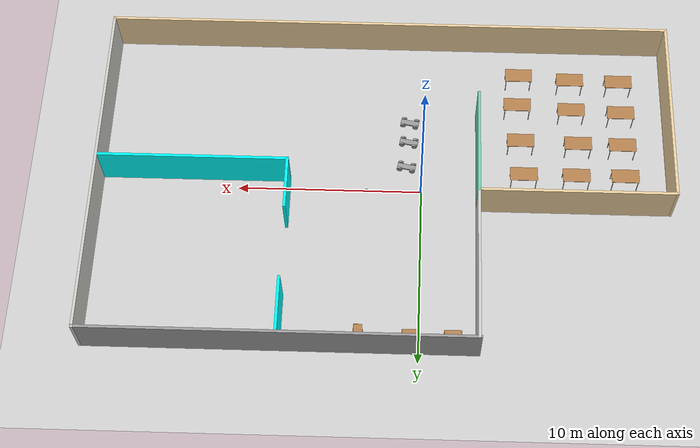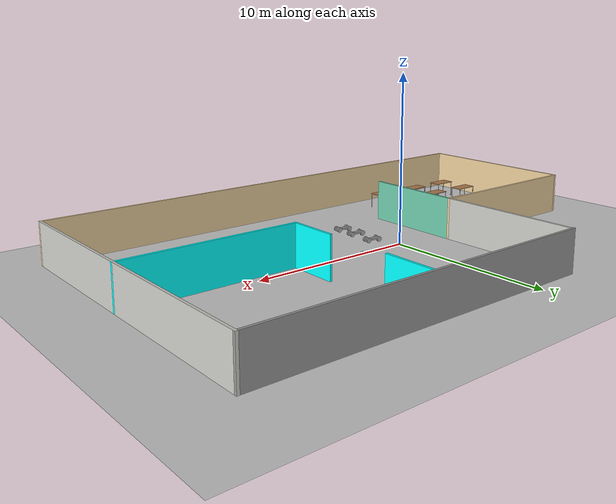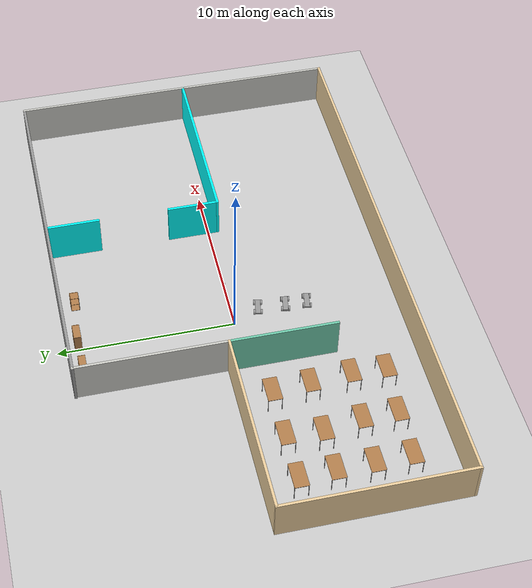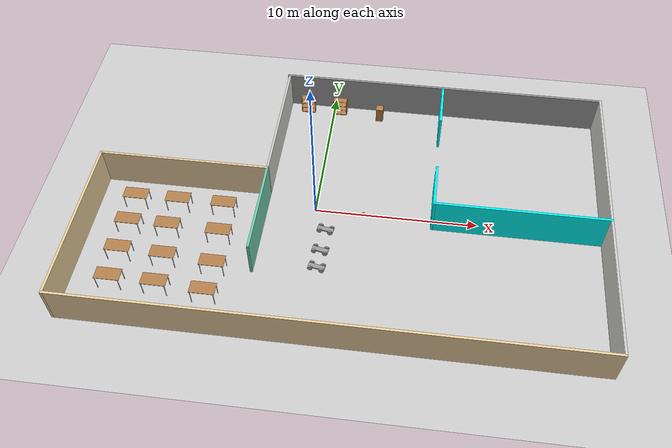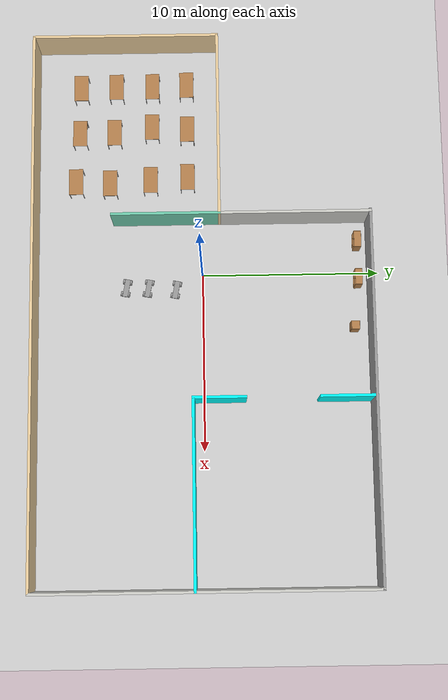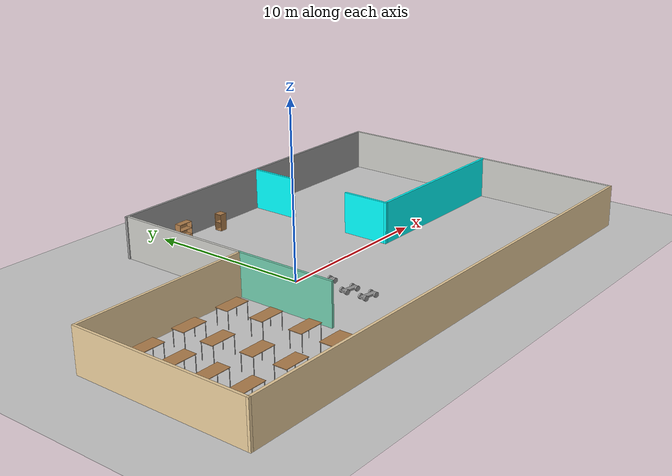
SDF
<sdf version="1.6">
 <world name="default">
  <plugin name="hello" filename="libhello.so"/>
  <light name="sun" type="directional">
   <pose>0 0 10 0 -0 0</pose>
   <diffuse>0.8 0.8 0.8 1</diffuse>
   <specular>0.2 0.2 0.2 1</specular>
   <attenuation>
    <range>1000</range>
    <constant>0.9</constant>
    <linear>0.01</linear>
    <quadratic>0.001</quadratic>
   </attenuation>
   <direction>-0.5 0.1 -0.9</direction>
  </light>
  <model name="ground_plane">
   <static>1</static>
   <link name="link">
    <collision name="collision">
     <geometry><plane><normal>0 0 1</normal><size>100 100</size></plane></geometry>
     <surface>
      <contact><collide_bitmask>65535</collide_bitmask></contact>
      <friction><ode><mu>100</mu><mu2>50</mu2></ode></friction>
     </surface>
    </collision>
    <visual name="visual">
     <cast_shadows>0</cast_shadows>
     <geometry><plane><normal>0 0 1</normal><size>100 100</size></plane></geometry>
     <material>
      <script><uri>file://media/materials/scripts/gazebo.material</uri><name>Gazebo/Grey</name></script>
     </material>
    </visual>
   </link>
  </model>
  <gravity>0 0 -9.8</gravity>
  <magnetic_field>6e-06 2.3e-05 -4.2e-05</magnetic_field>
  <atmosphere type="adiabatic"/>
  <physics name="default_physics" default="0" type="ode">
   <max_step_size>0.001</max_step_size>
   <real_time_factor>1</real_time_factor>
   <real_time_update_rate>1000</real_time_update_rate>
  </physics>
  <scene><ambient>0.4 0.4 0.4 1</ambient><background>0.7 0.7 0.7 1</background><shadows>1</shadows></scene>
  <spherical_coordinates>
   <surface_model>EARTH_WGS84</surface_model>
   <latitude_deg>0</latitude_deg>
   <longitude_deg>0</longitude_deg>
   <elevation>0</elevation>
   <heading_deg>0</heading_deg>
  </spherical_coordinates>
  <model name="building">
   <pose>1.986 0.00092 0 0 -0 0</pose>
   <link name="Wall_10">
    <collision name="Wall_10_Collision">
     <geometry><box><size>6.15 0.15 2.5</size></box></geometry>
     <pose>0 0 1.25 0 -0 0</pose>
    </collision>
    <visual name="Wall_10_Visual">
     <pose>0 0 1.25 0 -0 0</pose>
     <geometry><box><size>6.15 0.15 2.5</size></box></geometry>
     <material>
      <script><uri>file://media/materials/scripts/gazebo.material</uri><name>Gazebo/Grey</name></script>
      <ambient>0.435294 0.796078 0.67451 1</ambient>
     </material>
     <meta><layer>0</layer></meta>
    </visual>
    <pose>-5.063 -2.00092 0 0 0 -1.5708</pose>
   </link>
   <link name="Wall_12">
    <collision name="Wall_12_Collision">
     <geometry><box><size>10.4574 0.15 2.5</size></box></geometry>
     <pose>0 0 1.25 0 -0 0</pose>
    </collision>
    <visual name="Wall_12_Visual">
     <pose>0 0 1.25 0 -0 0</pose>
     <geometry><box><size>10.4574 0.15 2.5</size></box></geometry>
     <material>
      <script><uri>file://media/materials/scripts/gazebo.material</uri><name>Gazebo/Grey</name></script>
      <ambient>0 1 1 1</ambient>
     </material>
     <meta><layer>0</layer></meta>
    </visual>
    <pose>10.3965 -0.568923 0 0 -0 3.14159</pose>
   </link>
   <link name="Wall_13">
    <collision name="Wall_13_Collision">
     <geometry><box><size>3 0.15 2.5</size></box></geometry>
     <pose>0 0 1.25 0 -0 0</pose>
    </collision>
    <visual name="Wall_13_Visual">
     <pose>0 0 1.25 0 -0 0</pose>
     <geometry><box><size>3 0.15 2.5</size></box></geometry>
     <material>
      <script><uri>file://media/materials/scripts/gazebo.material</uri><name>Gazebo/Grey</name></script>
      <ambient>0 1 1 1</ambient>
     </material>
     <meta><layer>0</layer></meta>
    </visual>
    <pose>5.24289 0.856077 0 0 -0 1.57087</pose>
   </link>
   <link name="Wall_15">
    <collision name="Wall_15_Collision">
     <geometry><box><size>3 0.15 2.5</size></box></geometry>
     <pose>0 0 1.25 0 -0 0</pose>
    </collision>
    <visual name="Wall_15_Visual">
     <pose>0 0 1.25 0 -0 0</pose>
     <geometry><box><size>3 0.15 2.5</size></box></geometry>
     <material>
      <script><uri>file://media/materials/scripts/gazebo.material</uri><name>Gazebo/Grey</name></script>
      <ambient>0 1 1 1</ambient>
     </material>
     <meta><layer>0</layer></meta>
    </visual>
    <pose>5.25855 7.85224 0 0 0 -1.5708</pose>
   </link>
   <link name="Wall_3">
    <collision name="Wall_3_Collision">
     <geometry><box><size>10.5741 0.15 2.5</size></box></geometry>
     <pose>0 0 1.25 0 -0 0</pose>
    </collision>
    <visual name="Wall_3_Visual">
     <pose>0 0 1.25 0 -0 0</pose>
     <geometry><box><size>10.5741 0.15 2.5</size></box></geometry>
     <material>
      <script><uri>file://media/materials/scripts/gazebo.material</uri><name>Gazebo/Grey</name></script>
      <ambient>0.921569 0.807843 0.615686 1</ambient>
     </material>
     <meta><layer>0</layer></meta>
    </visual>
    <pose>-15.55 -4.21292 0 0 0 -1.5708</pose>
   </link>
   <link name="Wall_4">
    <collision name="Wall_4_Collision">
     <geometry><box><size>31.25 0.15 2.5</size></box></geometry>
     <pose>0 0 1.25 0 -0 0</pose>
    </collision>
    <visual name="Wall_4_Visual">
     <pose>0 0 1.25 0 -0 0</pose>
     <geometry><box><size>31.25 0.15 2.5</size></box></geometry>
     <material>
      <script><uri>file://media/materials/scripts/gazebo.material</uri><name>Gazebo/Grey</name></script>
      <ambient>0.921569 0.807843 0.615686 1</ambient>
     </material>
     <meta><layer>0</layer></meta>
    </visual>
    <pose>-0.000188 -9.42496 0 0 0 -3e-06</pose>
   </link>
   <link name="Wall_5">
    <collision name="Wall_5_Collision">
     <geometry><box><size>19 0.15 2.5</size></box></geometry>
     <pose>0 0 1.25 0 -0 0</pose>
    </collision>
    <visual name="Wall_5_Visual">
     <pose>0 0 1.25 0 -0 0</pose>
     <geometry><box><size>19 0.15 2.5</size></box></geometry>
     <material>
      <script><uri>file://media/materials/scripts/gazebo.material</uri><name>Gazebo/CeilingTiled</name></script>
      <ambient>1 1 1 1</ambient>
     </material>
     <meta><layer>0</layer></meta>
    </visual>
    <pose>15.5496 -1e-06 0 0 -0 1.5708</pose>
   </link>
   <link name="Wall_6">
    <collision name="Wall_6_Collision">
     <geometry><box><size>20.8246 0.15 2.5</size></box></geometry>
     <pose>0 0 1.25 0 -0 0</pose>
    </collision>
    <visual name="Wall_6_Visual">
     <pose>0 0 1.25 0 -0 0</pose>
     <geometry><box><size>20.8246 0.15 2.5</size></box></geometry>
     <material>
      <script><uri>file://media/materials/scripts/gazebo.material</uri><name>Gazebo/Grey</name></script>
      <ambient>1 1 1 1</ambient>
     </material>
     <meta><layer>0</layer></meta>
    </visual>
    <pose>5.21234 9.425 0 0 -0 3.14159</pose>
   </link>
   <link name="Wall_7">
    <collision name="Wall_7_Collision">
     <geometry><box><size>8.57592 0.15 2.5</size></box></geometry>
     <pose>0 0 1.25 0 -0 0</pose>
    </collision>
    <visual name="Wall_7_Visual">
     <pose>0 0 1.25 0 -0 0</pose>
     <geometry><box><size>8.57592 0.15 2.5</size></box></geometry>
     <material>
      <script><uri>file://media/materials/scripts/gazebo.material</uri><name>Gazebo/CeilingTiled</name></script>
      <ambient>1 1 1 1</ambient>
     </material>
     <meta><layer>0</layer></meta>
    </visual>
    <pose>-5.06321 5.21204 0 0 0 -1.57075</pose>
   </link>
   <link name="Wall_8">
    <collision name="Wall_8_Collision">
     <geometry><box><size>10.5754 0.15 2.5</size></box></geometry>
     <pose>0 0 1.25 0 -0 0</pose>
    </collision>
    <visual name="Wall_8_Visual">
     <pose>0 0 1.25 0 -0 0</pose>
     <geometry><box><size>10.5754 0.15 2.5</size></box></geometry>
     <material>
      <script><uri>file://media/materials/scripts/gazebo.material</uri><name>Gazebo/Grey</name></script>
      <ambient>0.921569 0.807843 0.615686 1</ambient>
     </material>
     <meta><layer>0</layer></meta>
    </visual>
    <pose>-10.2755 0.999077 0 0 -0 3.14159</pose>
   </link>
   <static>1</static>
  </model>
  <model name="table">
   <static>1</static>
   <link name="link">
    <collision name="surface">
     <pose>0 0 1 0 -0 0</pose>
     <geometry><box><size>1.5 0.8 0.03</size></box></geometry>
     <surface><friction><ode><mu>0.6</mu><mu2>0.6</mu2></ode></friction></surface>
    </collision>
    <visual name="visual1">
     <pose>0 0 1 0 -0 0</pose>
     <geometry><box><size>1.5 0.8 0.03</size></box></geometry>
     <material>
      <script><uri>file://media/materials/scripts/gazebo.material</uri><name>Gazebo/Wood</name></script>
     </material>
    </visual>
    <collision name="front_left_leg">
     <pose>0.68 0.38 0.5 0 -0 0</pose>
     <geometry><cylinder><radius>0.02</radius><length>1</length></cylinder></geometry>
    </collision>
    <visual name="front_left_leg">
     <pose>0.68 0.38 0.5 0 -0 0</pose>
     <geometry><cylinder><radius>0.02</radius><length>1</length></cylinder></geometry>
     <material>
      <script><uri>file://media/materials/scripts/gazebo.material</uri><name>Gazebo/Grey</name></script>
     </material>
    </visual>
    <collision name="front_right_leg">
     <pose>0.68 -0.38 0.5 0 -0 0</pose>
     <geometry><cylinder><radius>0.02</radius><length>1</length></cylinder></geometry>
    </collision>
    <visual name="front_right_leg">
     <pose>0.68 -0.38 0.5 0 -0 0</pose>
     <geometry><cylinder><radius>0.02</radius><length>1</length></cylinder></geometry>
     <material>
      <script><uri>file://media/materials/scripts/gazebo.material</uri><name>Gazebo/Grey</name></script>
     </material>
    </visual>
    <collision name="back_right_leg">
     <pose>-0.68 -0.38 0.5 0 -0 0</pose>
     <geometry><cylinder><radius>0.02</radius><length>1</length></cylinder></geometry>
    </collision>
    <visual name="back_right_leg">
     <pose>-0.68 -0.38 0.5 0 -0 0</pose>
     <geometry><cylinder><radius>0.02</radius><length>1</length></cylinder></geometry>
     <material>
      <script><uri>file://media/materials/scripts/gazebo.material</uri><name>Gazebo/Grey</name></script>
     </material>
    </visual>
    <collision name="back_left_leg">
     <pose>-0.68 0.38 0.5 0 -0 0</pose>
     <geometry><cylinder><radius>0.02</radius><length>1</length></cylinder></geometry>
    </collision>
    <visual name="back_left_leg">
     <pose>-0.68 0.38 0.5 0 -0 0</pose>
     <geometry><cylinder><radius>0.02</radius><length>1</length></cylinder></geometry>
     <material>
      <script><uri>file://media/materials/scripts/gazebo.material</uri><name>Gazebo/Grey</name></script>
     </material>
    </visual>
   </link>
   <pose>-11.1076 -0.793814 0 0 -0 0</pose>
  </model>
  <model name="table_0">
   <static>1</static>
   <link name="link">
    <collision name="surface">
     <pose>0 0 1 0 -0 0</pose>
     <geometry><box><size>1.5 0.8 0.03</size></box></geometry>
     <surface><friction><ode><mu>0.6</mu><mu2>0.6</mu2></ode></friction></surface>
    </collision>
    <visual name="visual1">
     <pose>0 0 1 0 -0 0</pose>
     <geometry><box><size>1.5 0.8 0.03</size></box></geometry>
     <material>
      <script><uri>file://media/materials/scripts/gazebo.material</uri><name>Gazebo/Wood</name></script>
     </material>
    </visual>
    <collision name="front_left_leg">
     <pose>0.68 0.38 0.5 0 -0 0</pose>
     <geometry><cylinder><radius>0.02</radius><length>1</length></cylinder></geometry>
    </collision>
    <visual name="front_left_leg">
     <pose>0.68 0.38 0.5 0 -0 0</pose>
     <geometry><cylinder><radius>0.02</radius><length>1</length></cylinder></geometry>
     <material>
      <script><uri>file://media/materials/scripts/gazebo.material</uri><name>Gazebo/Grey</name></script>
     </material>
    </visual>
    <collision name="front_right_leg">
     <pose>0.68 -0.38 0.5 0 -0 0</pose>
     <geometry><cylinder><radius>0.02</radius><length>1</length></cylinder></geometry>
    </collision>
    <visual name="front_right_leg">
     <pose>0.68 -0.38 0.5 0 -0 0</pose>
     <geometry><cylinder><radius>0.02</radius><length>1</length></cylinder></geometry>
     <material>
      <script><uri>file://media/materials/scripts/gazebo.material</uri><name>Gazebo/Grey</name></script>
     </material>
    </visual>
    <collision name="back_right_leg">
     <pose>-0.68 -0.38 0.5 0 -0 0</pose>
     <geometry><cylinder><radius>0.02</radius><length>1</length></cylinder></geometry>
    </collision>
    <visual name="back_right_leg">
     <pose>-0.68 -0.38 0.5 0 -0 0</pose>
     <geometry><cylinder><radius>0.02</radius><length>1</length></cylinder></geometry>
     <material>
      <script><uri>file://media/materials/scripts/gazebo.material</uri><name>Gazebo/Grey</name></script>
     </material>
    </visual>
    <collision name="back_left_leg">
     <pose>-0.68 0.38 0.5 0 -0 0</pose>
     <geometry><cylinder><radius>0.02</radius><length>1</length></cylinder></geometry>
    </collision>
    <visual name="back_left_leg">
     <pose>-0.68 0.38 0.5 0 -0 0</pose>
     <geometry><cylinder><radius>0.02</radius><length>1</length></cylinder></geometry>
     <material>
      <script><uri>file://media/materials/scripts/gazebo.material</uri><name>Gazebo/Grey</name></script>
     </material>
    </visual>
   </link>
   <pose>-11.0443 -2.76264 0 0 -0 0</pose>
  </model>
  <model name="table_1">
   <static>1</static>
   <link name="link">
    <collision name="surface">
     <pose>0 0 1 0 -0 0</pose>
     <geometry><box><size>1.5 0.8 0.03</size></box></geometry>
     <surface><friction><ode><mu>0.6</mu><mu2>0.6</mu2></ode></friction></surface>
    </collision>
    <visual name="visual1">
     <pose>0 0 1 0 -0 0</pose>
     <geometry><box><size>1.5 0.8 0.03</size></box></geometry>
     <material>
      <script><uri>file://media/materials/scripts/gazebo.material</uri><name>Gazebo/Wood</name></script>
     </material>
    </visual>
    <collision name="front_left_leg">
     <pose>0.68 0.38 0.5 0 -0 0</pose>
     <geometry><cylinder><radius>0.02</radius><length>1</length></cylinder></geometry>
    </collision>
    <visual name="front_left_leg">
     <pose>0.68 0.38 0.5 0 -0 0</pose>
     <geometry><cylinder><radius>0.02</radius><length>1</length></cylinder></geometry>
     <material>
      <script><uri>file://media/materials/scripts/gazebo.material</uri><name>Gazebo/Grey</name></script>
     </material>
    </visual>
    <collision name="front_right_leg">
     <pose>0.68 -0.38 0.5 0 -0 0</pose>
     <geometry><cylinder><radius>0.02</radius><length>1</length></cylinder></geometry>
    </collision>
    <visual name="front_right_leg">
     <pose>0.68 -0.38 0.5 0 -0 0</pose>
     <geometry><cylinder><radius>0.02</radius><length>1</length></cylinder></geometry>
     <material>
      <script><uri>file://media/materials/scripts/gazebo.material</uri><name>Gazebo/Grey</name></script>
     </material>
    </visual>
    <collision name="back_right_leg">
     <pose>-0.68 -0.38 0.5 0 -0 0</pose>
     <geometry><cylinder><radius>0.02</radius><length>1</length></cylinder></geometry>
    </collision>
    <visual name="back_right_leg">
     <pose>-0.68 -0.38 0.5 0 -0 0</pose>
     <geometry><cylinder><radius>0.02</radius><length>1</length></cylinder></geometry>
     <material>
      <script><uri>file://media/materials/scripts/gazebo.material</uri><name>Gazebo/Grey</name></script>
     </material>
    </visual>
    <collision name="back_left_leg">
     <pose>-0.68 0.38 0.5 0 -0 0</pose>
     <geometry><cylinder><radius>0.02</radius><length>1</length></cylinder></geometry>
    </collision>
    <visual name="back_left_leg">
     <pose>-0.68 0.38 0.5 0 -0 0</pose>
     <geometry><cylinder><radius>0.02</radius><length>1</length></cylinder></geometry>
     <material>
      <script><uri>file://media/materials/scripts/gazebo.material</uri><name>Gazebo/Grey</name></script>
     </material>
    </visual>
   </link>
   <pose>-11.0405 -4.83627 0 0 -0 0</pose>
  </model>
  <model name="table_2">
   <static>1</static>
   <link name="link">
    <collision name="surface">
     <pose>0 0 1 0 -0 0</pose>
     <geometry><box><size>1.5 0.8 0.03</size></box></geometry>
     <surface><friction><ode><mu>0.6</mu><mu2>0.6</mu2></ode></friction></surface>
    </collision>
    <visual name="visual1">
     <pose>0 0 1 0 -0 0</pose>
     <geometry><box><size>1.5 0.8 0.03</size></box></geometry>
     <material>
      <script><uri>file://media/materials/scripts/gazebo.material</uri><name>Gazebo/Wood</name></script>
     </material>
    </visual>
    <collision name="front_left_leg">
     <pose>0.68 0.38 0.5 0 -0 0</pose>
     <geometry><cylinder><radius>0.02</radius><length>1</length></cylinder></geometry>
    </collision>
    <visual name="front_left_leg">
     <pose>0.68 0.38 0.5 0 -0 0</pose>
     <geometry><cylinder><radius>0.02</radius><length>1</length></cylinder></geometry>
     <material>
      <script><uri>file://media/materials/scripts/gazebo.material</uri><name>Gazebo/Grey</name></script>
     </material>
    </visual>
    <collision name="front_right_leg">
     <pose>0.68 -0.38 0.5 0 -0 0</pose>
     <geometry><cylinder><radius>0.02</radius><length>1</length></cylinder></geometry>
    </collision>
    <visual name="front_right_leg">
     <pose>0.68 -0.38 0.5 0 -0 0</pose>
     <geometry><cylinder><radius>0.02</radius><length>1</length></cylinder></geometry>
     <material>
      <script><uri>file://media/materials/scripts/gazebo.material</uri><name>Gazebo/Grey</name></script>
     </material>
    </visual>
    <collision name="back_right_leg">
     <pose>-0.68 -0.38 0.5 0 -0 0</pose>
     <geometry><cylinder><radius>0.02</radius><length>1</length></cylinder></geometry>
    </collision>
    <visual name="back_right_leg">
     <pose>-0.68 -0.38 0.5 0 -0 0</pose>
     <geometry><cylinder><radius>0.02</radius><length>1</length></cylinder></geometry>
     <material>
      <script><uri>file://media/materials/scripts/gazebo.material</uri><name>Gazebo/Grey</name></script>
     </material>
    </visual>
    <collision name="back_left_leg">
     <pose>-0.68 0.38 0.5 0 -0 0</pose>
     <geometry><cylinder><radius>0.02</radius><length>1</length></cylinder></geometry>
    </collision>
    <visual name="back_left_leg">
     <pose>-0.68 0.38 0.5 0 -0 0</pose>
     <geometry><cylinder><radius>0.02</radius><length>1</length></cylinder></geometry>
     <material>
      <script><uri>file://media/materials/scripts/gazebo.material</uri><name>Gazebo/Grey</name></script>
     </material>
    </visual>
   </link>
   <pose>-10.9936 -6.86304 0 0 -0 0</pose>
  </model>
  <model name="table_3">
   <static>1</static>
   <link name="link">
    <collision name="surface">
     <pose>0 0 1 0 -0 0</pose>
     <geometry><box><size>1.5 0.8 0.03</size></box></geometry>
     <surface><friction><ode><mu>0.6</mu><mu2>0.6</mu2></ode></friction></surface>
    </collision>
    <visual name="visual1">
     <pose>0 0 1 0 -0 0</pose>
     <geometry><box><size>1.5 0.8 0.03</size></box></geometry>
     <material>
      <script><uri>file://media/materials/scripts/gazebo.material</uri><name>Gazebo/Wood</name></script>
     </material>
    </visual>
    <collision name="front_left_leg">
     <pose>0.68 0.38 0.5 0 -0 0</pose>
     <geometry><cylinder><radius>0.02</radius><length>1</length></cylinder></geometry>
    </collision>
    <visual name="front_left_leg">
     <pose>0.68 0.38 0.5 0 -0 0</pose>
     <geometry><cylinder><radius>0.02</radius><length>1</length></cylinder></geometry>
     <material>
      <script><uri>file://media/materials/scripts/gazebo.material</uri><name>Gazebo/Grey</name></script>
     </material>
    </visual>
    <collision name="front_right_leg">
     <pose>0.68 -0.38 0.5 0 -0 0</pose>
     <geometry><cylinder><radius>0.02</radius><length>1</length></cylinder></geometry>
    </collision>
    <visual name="front_right_leg">
     <pose>0.68 -0.38 0.5 0 -0 0</pose>
     <geometry><cylinder><radius>0.02</radius><length>1</length></cylinder></geometry>
     <material>
      <script><uri>file://media/materials/scripts/gazebo.material</uri><name>Gazebo/Grey</name></script>
     </material>
    </visual>
    <collision name="back_right_leg">
     <pose>-0.68 -0.38 0.5 0 -0 0</pose>
     <geometry><cylinder><radius>0.02</radius><length>1</length></cylinder></geometry>
    </collision>
    <visual name="back_right_leg">
     <pose>-0.68 -0.38 0.5 0 -0 0</pose>
     <geometry><cylinder><radius>0.02</radius><length>1</length></cylinder></geometry>
     <material>
      <script><uri>file://media/materials/scripts/gazebo.material</uri><name>Gazebo/Grey</name></script>
     </material>
    </visual>
    <collision name="back_left_leg">
     <pose>-0.68 0.38 0.5 0 -0 0</pose>
     <geometry><cylinder><radius>0.02</radius><length>1</length></cylinder></geometry>
    </collision>
    <visual name="back_left_leg">
     <pose>-0.68 0.38 0.5 0 -0 0</pose>
     <geometry><cylinder><radius>0.02</radius><length>1</length></cylinder></geometry>
     <material>
      <script><uri>file://media/materials/scripts/gazebo.material</uri><name>Gazebo/Grey</name></script>
     </material>
    </visual>
   </link>
   <pose>-8.45188 -0.777203 0 0 -0 0</pose>
  </model>
  <model name="table_4">
   <static>1</static>
   <link name="link">
    <collision name="surface">
     <pose>0 0 1 0 -0 0</pose>
     <geometry><box><size>1.5 0.8 0.03</size></box></geometry>
     <surface><friction><ode><mu>0.6</mu><mu2>0.6</mu2></ode></friction></surface>
    </collision>
    <visual name="visual1">
     <pose>0 0 1 0 -0 0</pose>
     <geometry><box><size>1.5 0.8 0.03</size></box></geometry>
     <material>
      <script><uri>file://media/materials/scripts/gazebo.material</uri><name>Gazebo/Wood</name></script>
     </material>
    </visual>
    <collision name="front_left_leg">
     <pose>0.68 0.38 0.5 0 -0 0</pose>
     <geometry><cylinder><radius>0.02</radius><length>1</length></cylinder></geometry>
    </collision>
    <visual name="front_left_leg">
     <pose>0.68 0.38 0.5 0 -0 0</pose>
     <geometry><cylinder><radius>0.02</radius><length>1</length></cylinder></geometry>
     <material>
      <script><uri>file://media/materials/scripts/gazebo.material</uri><name>Gazebo/Grey</name></script>
     </material>
    </visual>
    <collision name="front_right_leg">
     <pose>0.68 -0.38 0.5 0 -0 0</pose>
     <geometry><cylinder><radius>0.02</radius><length>1</length></cylinder></geometry>
    </collision>
    <visual name="front_right_leg">
     <pose>0.68 -0.38 0.5 0 -0 0</pose>
     <geometry><cylinder><radius>0.02</radius><length>1</length></cylinder></geometry>
     <material>
      <script><uri>file://media/materials/scripts/gazebo.material</uri><name>Gazebo/Grey</name></script>
     </material>
    </visual>
    <collision name="back_right_leg">
     <pose>-0.68 -0.38 0.5 0 -0 0</pose>
     <geometry><cylinder><radius>0.02</radius><length>1</length></cylinder></geometry>
    </collision>
    <visual name="back_right_leg">
     <pose>-0.68 -0.38 0.5 0 -0 0</pose>
     <geometry><cylinder><radius>0.02</radius><length>1</length></cylinder></geometry>
     <material>
      <script><uri>file://media/materials/scripts/gazebo.material</uri><name>Gazebo/Grey</name></script>
     </material>
    </visual>
    <collision name="back_left_leg">
     <pose>-0.68 0.38 0.5 0 -0 0</pose>
     <geometry><cylinder><radius>0.02</radius><length>1</length></cylinder></geometry>
    </collision>
    <visual name="back_left_leg">
     <pose>-0.68 0.38 0.5 0 -0 0</pose>
     <geometry><cylinder><radius>0.02</radius><length>1</length></cylinder></geometry>
     <material>
      <script><uri>file://media/materials/scripts/gazebo.material</uri><name>Gazebo/Grey</name></script>
     </material>
    </visual>
   </link>
   <pose>-8.60311 -2.79438 0 0 -0 0</pose>
  </model>
  <model name="table_5">
   <static>1</static>
   <link name="link">
    <collision name="surface">
     <pose>0 0 1 0 -0 0</pose>
     <geometry><box><size>1.5 0.8 0.03</size></box></geometry>
     <surface><friction><ode><mu>0.6</mu><mu2>0.6</mu2></ode></friction></surface>
    </collision>
    <visual name="visual1">
     <pose>0 0 1 0 -0 0</pose>
     <geometry><box><size>1.5 0.8 0.03</size></box></geometry>
     <material>
      <script><uri>file://media/materials/scripts/gazebo.material</uri><name>Gazebo/Wood</name></script>
     </material>
    </visual>
    <collision name="front_left_leg">
     <pose>0.68 0.38 0.5 0 -0 0</pose>
     <geometry><cylinder><radius>0.02</radius><length>1</length></cylinder></geometry>
    </collision>
    <visual name="front_left_leg">
     <pose>0.68 0.38 0.5 0 -0 0</pose>
     <geometry><cylinder><radius>0.02</radius><length>1</length></cylinder></geometry>
     <material>
      <script><uri>file://media/materials/scripts/gazebo.material</uri><name>Gazebo/Grey</name></script>
     </material>
    </visual>
    <collision name="front_right_leg">
     <pose>0.68 -0.38 0.5 0 -0 0</pose>
     <geometry><cylinder><radius>0.02</radius><length>1</length></cylinder></geometry>
    </collision>
    <visual name="front_right_leg">
     <pose>0.68 -0.38 0.5 0 -0 0</pose>
     <geometry><cylinder><radius>0.02</radius><length>1</length></cylinder></geometry>
     <material>
      <script><uri>file://media/materials/scripts/gazebo.material</uri><name>Gazebo/Grey</name></script>
     </material>
    </visual>
    <collision name="back_right_leg">
     <pose>-0.68 -0.38 0.5 0 -0 0</pose>
     <geometry><cylinder><radius>0.02</radius><length>1</length></cylinder></geometry>
    </collision>
    <visual name="back_right_leg">
     <pose>-0.68 -0.38 0.5 0 -0 0</pose>
     <geometry><cylinder><radius>0.02</radius><length>1</length></cylinder></geometry>
     <material>
      <script><uri>file://media/materials/scripts/gazebo.material</uri><name>Gazebo/Grey</name></script>
     </material>
    </visual>
    <collision name="back_left_leg">
     <pose>-0.68 0.38 0.5 0 -0 0</pose>
     <geometry><cylinder><radius>0.02</radius><length>1</length></cylinder></geometry>
    </collision>
    <visual name="back_left_leg">
     <pose>-0.68 0.38 0.5 0 -0 0</pose>
     <geometry><cylinder><radius>0.02</radius><length>1</length></cylinder></geometry>
     <material>
      <script><uri>file://media/materials/scripts/gazebo.material</uri><name>Gazebo/Grey</name></script>
     </material>
    </visual>
   </link>
   <pose>-8.28829 -4.96082 0 0 -0 0</pose>
  </model>
  <model name="table_6">
   <static>1</static>
   <link name="link">
    <collision name="surface">
     <pose>0 0 1 0 -0 0</pose>
     <geometry><box><size>1.5 0.8 0.03</size></box></geometry>
     <surface><friction><ode><mu>0.6</mu><mu2>0.6</mu2></ode></friction></surface>
    </collision>
    <visual name="visual1">
     <pose>0 0 1 0 -0 0</pose>
     <geometry><box><size>1.5 0.8 0.03</size></box></geometry>
     <material>
      <script><uri>file://media/materials/scripts/gazebo.material</uri><name>Gazebo/Wood</name></script>
     </material>
    </visual>
    <collision name="front_left_leg">
     <pose>0.68 0.38 0.5 0 -0 0</pose>
     <geometry><cylinder><radius>0.02</radius><length>1</length></cylinder></geometry>
    </collision>
    <visual name="front_left_leg">
     <pose>0.68 0.38 0.5 0 -0 0</pose>
     <geometry><cylinder><radius>0.02</radius><length>1</length></cylinder></geometry>
     <material>
      <script><uri>file://media/materials/scripts/gazebo.material</uri><name>Gazebo/Grey</name></script>
     </material>
    </visual>
    <collision name="front_right_leg">
     <pose>0.68 -0.38 0.5 0 -0 0</pose>
     <geometry><cylinder><radius>0.02</radius><length>1</length></cylinder></geometry>
    </collision>
    <visual name="front_right_leg">
     <pose>0.68 -0.38 0.5 0 -0 0</pose>
     <geometry><cylinder><radius>0.02</radius><length>1</length></cylinder></geometry>
     <material>
      <script><uri>file://media/materials/scripts/gazebo.material</uri><name>Gazebo/Grey</name></script>
     </material>
    </visual>
    <collision name="back_right_leg">
     <pose>-0.68 -0.38 0.5 0 -0 0</pose>
     <geometry><cylinder><radius>0.02</radius><length>1</length></cylinder></geometry>
    </collision>
    <visual name="back_right_leg">
     <pose>-0.68 -0.38 0.5 0 -0 0</pose>
     <geometry><cylinder><radius>0.02</radius><length>1</length></cylinder></geometry>
     <material>
      <script><uri>file://media/materials/scripts/gazebo.material</uri><name>Gazebo/Grey</name></script>
     </material>
    </visual>
    <collision name="back_left_leg">
     <pose>-0.68 0.38 0.5 0 -0 0</pose>
     <geometry><cylinder><radius>0.02</radius><length>1</length></cylinder></geometry>
    </collision>
    <visual name="back_left_leg">
     <pose>-0.68 0.38 0.5 0 -0 0</pose>
     <geometry><cylinder><radius>0.02</radius><length>1</length></cylinder></geometry>
     <material>
      <script><uri>file://media/materials/scripts/gazebo.material</uri><name>Gazebo/Grey</name></script>
     </material>
    </visual>
   </link>
   <pose>-8.26111 -6.92444 0 0 -0 0</pose>
  </model>
  <model name="table_7">
   <static>1</static>
   <link name="link">
    <collision name="surface">
     <pose>0 0 1 0 -0 0</pose>
     <geometry><box><size>1.5 0.8 0.03</size></box></geometry>
     <surface><friction><ode><mu>0.6</mu><mu2>0.6</mu2></ode></friction></surface>
    </collision>
    <visual name="visual1">
     <pose>0 0 1 0 -0 0</pose>
     <geometry><box><size>1.5 0.8 0.03</size></box></geometry>
     <material>
      <script><uri>file://media/materials/scripts/gazebo.material</uri><name>Gazebo/Wood</name></script>
     </material>
    </visual>
    <collision name="front_left_leg">
     <pose>0.68 0.38 0.5 0 -0 0</pose>
     <geometry><cylinder><radius>0.02</radius><length>1</length></cylinder></geometry>
    </collision>
    <visual name="front_left_leg">
     <pose>0.68 0.38 0.5 0 -0 0</pose>
     <geometry><cylinder><radius>0.02</radius><length>1</length></cylinder></geometry>
     <material>
      <script><uri>file://media/materials/scripts/gazebo.material</uri><name>Gazebo/Grey</name></script>
     </material>
    </visual>
    <collision name="front_right_leg">
     <pose>0.68 -0.38 0.5 0 -0 0</pose>
     <geometry><cylinder><radius>0.02</radius><length>1</length></cylinder></geometry>
    </collision>
    <visual name="front_right_leg">
     <pose>0.68 -0.38 0.5 0 -0 0</pose>
     <geometry><cylinder><radius>0.02</radius><length>1</length></cylinder></geometry>
     <material>
      <script><uri>file://media/materials/scripts/gazebo.material</uri><name>Gazebo/Grey</name></script>
     </material>
    </visual>
    <collision name="back_right_leg">
     <pose>-0.68 -0.38 0.5 0 -0 0</pose>
     <geometry><cylinder><radius>0.02</radius><length>1</length></cylinder></geometry>
    </collision>
    <visual name="back_right_leg">
     <pose>-0.68 -0.38 0.5 0 -0 0</pose>
     <geometry><cylinder><radius>0.02</radius><length>1</length></cylinder></geometry>
     <material>
      <script><uri>file://media/materials/scripts/gazebo.material</uri><name>Gazebo/Grey</name></script>
     </material>
    </visual>
    <collision name="back_left_leg">
     <pose>-0.68 0.38 0.5 0 -0 0</pose>
     <geometry><cylinder><radius>0.02</radius><length>1</length></cylinder></geometry>
    </collision>
    <visual name="back_left_leg">
     <pose>-0.68 0.38 0.5 0 -0 0</pose>
     <geometry><cylinder><radius>0.02</radius><length>1</length></cylinder></geometry>
     <material>
      <script><uri>file://media/materials/scripts/gazebo.material</uri><name>Gazebo/Grey</name></script>
     </material>
    </visual>
   </link>
   <pose>-5.58712 -0.783309 0 0 -0 0</pose>
  </model>
  <model name="table_8">
   <static>1</static>
   <link name="link">
    <collision name="surface">
     <pose>0 0 1 0 -0 0</pose>
     <geometry><box><size>1.5 0.8 0.03</size></box></geometry>
     <surface><friction><ode><mu>0.6</mu><mu2>0.6</mu2></ode></friction></surface>
    </collision>
    <visual name="visual1">
     <pose>0 0 1 0 -0 0</pose>
     <geometry><box><size>1.5 0.8 0.03</size></box></geometry>
     <material>
      <script><uri>file://media/materials/scripts/gazebo.material</uri><name>Gazebo/Wood</name></script>
     </material>
    </visual>
    <collision name="front_left_leg">
     <pose>0.68 0.38 0.5 0 -0 0</pose>
     <geometry><cylinder><radius>0.02</radius><length>1</length></cylinder></geometry>
    </collision>
    <visual name="front_left_leg">
     <pose>0.68 0.38 0.5 0 -0 0</pose>
     <geometry><cylinder><radius>0.02</radius><length>1</length></cylinder></geometry>
     <material>
      <script><uri>file://media/materials/scripts/gazebo.material</uri><name>Gazebo/Grey</name></script>
     </material>
    </visual>
    <collision name="front_right_leg">
     <pose>0.68 -0.38 0.5 0 -0 0</pose>
     <geometry><cylinder><radius>0.02</radius><length>1</length></cylinder></geometry>
    </collision>
    <visual name="front_right_leg">
     <pose>0.68 -0.38 0.5 0 -0 0</pose>
     <geometry><cylinder><radius>0.02</radius><length>1</length></cylinder></geometry>
     <material>
      <script><uri>file://media/materials/scripts/gazebo.material</uri><name>Gazebo/Grey</name></script>
     </material>
    </visual>
    <collision name="back_right_leg">
     <pose>-0.68 -0.38 0.5 0 -0 0</pose>
     <geometry><cylinder><radius>0.02</radius><length>1</length></cylinder></geometry>
    </collision>
    <visual name="back_right_leg">
     <pose>-0.68 -0.38 0.5 0 -0 0</pose>
     <geometry><cylinder><radius>0.02</radius><length>1</length></cylinder></geometry>
     <material>
      <script><uri>file://media/materials/scripts/gazebo.material</uri><name>Gazebo/Grey</name></script>
     </material>
    </visual>
    <collision name="back_left_leg">
     <pose>-0.68 0.38 0.5 0 -0 0</pose>
     <geometry><cylinder><radius>0.02</radius><length>1</length></cylinder></geometry>
    </collision>
    <visual name="back_left_leg">
     <pose>-0.68 0.38 0.5 0 -0 0</pose>
     <geometry><cylinder><radius>0.02</radius><length>1</length></cylinder></geometry>
     <material>
      <script><uri>file://media/materials/scripts/gazebo.material</uri><name>Gazebo/Grey</name></script>
     </material>
    </visual>
   </link>
   <pose>-5.43799 -2.9013 0 0 -0 0</pose>
  </model>
  <model name="table_9">
   <static>1</static>
   <link name="link">
    <collision name="surface">
     <pose>0 0 1 0 -0 0</pose>
     <geometry><box><size>1.5 0.8 0.03</size></box></geometry>
     <surface><friction><ode><mu>0.6</mu><mu2>0.6</mu2></ode></friction></surface>
    </collision>
    <visual name="visual1">
     <pose>0 0 1 0 -0 0</pose>
     <geometry><box><size>1.5 0.8 0.03</size></box></geometry>
     <material>
      <script><uri>file://media/materials/scripts/gazebo.material</uri><name>Gazebo/Wood</name></script>
     </material>
    </visual>
    <collision name="front_left_leg">
     <pose>0.68 0.38 0.5 0 -0 0</pose>
     <geometry><cylinder><radius>0.02</radius><length>1</length></cylinder></geometry>
    </collision>
    <visual name="front_left_leg">
     <pose>0.68 0.38 0.5 0 -0 0</pose>
     <geometry><cylinder><radius>0.02</radius><length>1</length></cylinder></geometry>
     <material>
      <script><uri>file://media/materials/scripts/gazebo.material</uri><name>Gazebo/Grey</name></script>
     </material>
    </visual>
    <collision name="front_right_leg">
     <pose>0.68 -0.38 0.5 0 -0 0</pose>
     <geometry><cylinder><radius>0.02</radius><length>1</length></cylinder></geometry>
    </collision>
    <visual name="front_right_leg">
     <pose>0.68 -0.38 0.5 0 -0 0</pose>
     <geometry><cylinder><radius>0.02</radius><length>1</length></cylinder></geometry>
     <material>
      <script><uri>file://media/materials/scripts/gazebo.material</uri><name>Gazebo/Grey</name></script>
     </material>
    </visual>
    <collision name="back_right_leg">
     <pose>-0.68 -0.38 0.5 0 -0 0</pose>
     <geometry><cylinder><radius>0.02</radius><length>1</length></cylinder></geometry>
    </collision>
    <visual name="back_right_leg">
     <pose>-0.68 -0.38 0.5 0 -0 0</pose>
     <geometry><cylinder><radius>0.02</radius><length>1</length></cylinder></geometry>
     <material>
      <script><uri>file://media/materials/scripts/gazebo.material</uri><name>Gazebo/Grey</name></script>
     </material>
    </visual>
    <collision name="back_left_leg">
     <pose>-0.68 0.38 0.5 0 -0 0</pose>
     <geometry><cylinder><radius>0.02</radius><length>1</length></cylinder></geometry>
    </collision>
    <visual name="back_left_leg">
     <pose>-0.68 0.38 0.5 0 -0 0</pose>
     <geometry><cylinder><radius>0.02</radius><length>1</length></cylinder></geometry>
     <material>
      <script><uri>file://media/materials/scripts/gazebo.material</uri><name>Gazebo/Grey</name></script>
     </material>
    </visual>
   </link>
   <pose>-5.28318 -5.20551 0 0 -0 0</pose>
  </model>
  <model name="table_10">
   <static>1</static>
   <link name="link">
    <collision name="surface">
     <pose>0 0 1 0 -0 0</pose>
     <geometry><box><size>1.5 0.8 0.03</size></box></geometry>
     <surface><friction><ode><mu>0.6</mu><mu2>0.6</mu2></ode></friction></surface>
    </collision>
    <visual name="visual1">
     <pose>0 0 1 0 -0 0</pose>
     <geometry><box><size>1.5 0.8 0.03</size></box></geometry>
     <material>
      <script><uri>file://media/materials/scripts/gazebo.material</uri><name>Gazebo/Wood</name></script>
     </material>
    </visual>
    <collision name="front_left_leg">
     <pose>0.68 0.38 0.5 0 -0 0</pose>
     <geometry><cylinder><radius>0.02</radius><length>1</length></cylinder></geometry>
    </collision>
    <visual name="front_left_leg">
     <pose>0.68 0.38 0.5 0 -0 0</pose>
     <geometry><cylinder><radius>0.02</radius><length>1</length></cylinder></geometry>
     <material>
      <script><uri>file://media/materials/scripts/gazebo.material</uri><name>Gazebo/Grey</name></script>
     </material>
    </visual>
    <collision name="front_right_leg">
     <pose>0.68 -0.38 0.5 0 -0 0</pose>
     <geometry><cylinder><radius>0.02</radius><length>1</length></cylinder></geometry>
    </collision>
    <visual name="front_right_leg">
     <pose>0.68 -0.38 0.5 0 -0 0</pose>
     <geometry><cylinder><radius>0.02</radius><length>1</length></cylinder></geometry>
     <material>
      <script><uri>file://media/materials/scripts/gazebo.material</uri><name>Gazebo/Grey</name></script>
     </material>
    </visual>
    <collision name="back_right_leg">
     <pose>-0.68 -0.38 0.5 0 -0 0</pose>
     <geometry><cylinder><radius>0.02</radius><length>1</length></cylinder></geometry>
    </collision>
    <visual name="back_right_leg">
     <pose>-0.68 -0.38 0.5 0 -0 0</pose>
     <geometry><cylinder><radius>0.02</radius><length>1</length></cylinder></geometry>
     <material>
      <script><uri>file://media/materials/scripts/gazebo.material</uri><name>Gazebo/Grey</name></script>
     </material>
    </visual>
    <collision name="back_left_leg">
     <pose>-0.68 0.38 0.5 0 -0 0</pose>
     <geometry><cylinder><radius>0.02</radius><length>1</length></cylinder></geometry>
    </collision>
    <visual name="back_left_leg">
     <pose>-0.68 0.38 0.5 0 -0 0</pose>
     <geometry><cylinder><radius>0.02</radius><length>1</length></cylinder></geometry>
     <material>
      <script><uri>file://media/materials/scripts/gazebo.material</uri><name>Gazebo/Grey</name></script>
     </material>
    </visual>
   </link>
   <pose>-5.37537 -7.1441 0 0 -0 0</pose>
  </model>
  <model name="bookshelf">
   <static>1</static>
   <link name="link">
    <inertial><mass>1</mass></inertial>
    <collision name="back">
     <pose>0 0.005 0.6 0 -0 0</pose>
     <geometry><box><size>0.9 0.01 1.2</size></box></geometry>
    </collision>
    <visual name="visual1">
     <pose>0 0.005 0.6 0 -0 0</pose>
     <geometry><box><size>0.9 0.01 1.2</size></box></geometry>
     <material>
      <script><uri>file://media/materials/scripts/gazebo.material</uri><name>Gazebo/Wood</name></script>
     </material>
    </visual>
    <collision name="left_side">
     <pose>0.45 -0.195 0.6 0 -0 0</pose>
     <geometry><box><size>0.02 0.4 1.2</size></box></geometry>
    </collision>
    <visual name="visual2">
     <pose>0.45 -0.195 0.6 0 -0 0</pose>
     <geometry><box><size>0.02 0.4 1.2</size></box></geometry>
     <material>
      <script><uri>file://media/materials/scripts/gazebo.material</uri><name>Gazebo/Wood</name></script>
     </material>
    </visual>
    <collision name="right_side">
     <pose>-0.45 -0.195 0.6 0 -0 0</pose>
     <geometry><box><size>0.02 0.4 1.2</size></box></geometry>
    </collision>
    <visual name="visual3">
     <pose>-0.45 -0.195 0.6 0 -0 0</pose>
     <geometry><box><size>0.02 0.4 1.2</size></box></geometry>
     <material>
      <script><uri>file://media/materials/scripts/gazebo.material</uri><name>Gazebo/Wood</name></script>
     </material>
    </visual>
    <collision name="bottom">
     <pose>0 -0.195 0.03 0 -0 0</pose>
     <geometry><box><size>0.88 0.4 0.06</size></box></geometry>
    </collision>
    <visual name="visual4">
     <pose>0 -0.195 0.03 0 -0 0</pose>
     <geometry><box><size>0.88 0.4 0.06</size></box></geometry>
     <material>
      <script><uri>file://media/materials/scripts/gazebo.material</uri><name>Gazebo/Wood</name></script>
     </material>
    </visual>
    <collision name="top">
     <pose>0 -0.195 1.19 0 -0 0</pose>
     <geometry><box><size>0.88 0.4 0.02</size></box></geometry>
    </collision>
    <visual name="visual5">
     <pose>0 -0.195 1.19 0 -0 0</pose>
     <geometry><box><size>0.88 0.4 0.02</size></box></geometry>
     <material>
      <script><uri>file://media/materials/scripts/gazebo.material</uri><name>Gazebo/Wood</name></script>
     </material>
    </visual>
    <collision name="low_shelf">
     <pose>0 -0.195 0.43 0 -0 0</pose>
     <geometry><box><size>0.88 0.4 0.02</size></box></geometry>
    </collision>
    <visual name="visual6">
     <pose>0 -0.195 0.43 0 -0 0</pose>
     <geometry><box><size>0.88 0.4 0.02</size></box></geometry>
     <material>
      <script><uri>file://media/materials/scripts/gazebo.material</uri><name>Gazebo/Wood</name></script>
     </material>
    </visual>
    <collision name="high_shelf">
     <pose>0 -0.195 0.8 0 -0 0</pose>
     <geometry><box><size>0.88 0.4 0.02</size></box></geometry>
    </collision>
    <visual name="visual7">
     <pose>0 -0.195 0.8 0 -0 0</pose>
     <geometry><box><size>0.88 0.4 0.02</size></box></geometry>
     <material>
      <script><uri>file://media/materials/scripts/gazebo.material</uri><name>Gazebo/Wood</name></script>
     </material>
    </visual>
   </link>
   <pose>-1.77258 8.9835 0 0 -0 0</pose>
  </model>
  <model name="bookshelf_0">
   <static>1</static>
   <link name="link">
    <inertial><mass>1</mass></inertial>
    <collision name="back">
     <pose>0 0.005 0.6 0 -0 0</pose>
     <geometry><box><size>0.9 0.01 1.2</size></box></geometry>
    </collision>
    <visual name="visual1">
     <pose>0 0.005 0.6 0 -0 0</pose>
     <geometry><box><size>0.9 0.01 1.2</size></box></geometry>
     <material>
      <script><uri>file://media/materials/scripts/gazebo.material</uri><name>Gazebo/Wood</name></script>
     </material>
    </visual>
    <collision name="left_side">
     <pose>0.45 -0.195 0.6 0 -0 0</pose>
     <geometry><box><size>0.02 0.4 1.2</size></box></geometry>
    </collision>
    <visual name="visual2">
     <pose>0.45 -0.195 0.6 0 -0 0</pose>
     <geometry><box><size>0.02 0.4 1.2</size></box></geometry>
     <material>
      <script><uri>file://media/materials/scripts/gazebo.material</uri><name>Gazebo/Wood</name></script>
     </material>
    </visual>
    <collision name="right_side">
     <pose>-0.45 -0.195 0.6 0 -0 0</pose>
     <geometry><box><size>0.02 0.4 1.2</size></box></geometry>
    </collision>
    <visual name="visual3">
     <pose>-0.45 -0.195 0.6 0 -0 0</pose>
     <geometry><box><size>0.02 0.4 1.2</size></box></geometry>
     <material>
      <script><uri>file://media/materials/scripts/gazebo.material</uri><name>Gazebo/Wood</name></script>
     </material>
    </visual>
    <collision name="bottom">
     <pose>0 -0.195 0.03 0 -0 0</pose>
     <geometry><box><size>0.88 0.4 0.06</size></box></geometry>
    </collision>
    <visual name="visual4">
     <pose>0 -0.195 0.03 0 -0 0</pose>
     <geometry><box><size>0.88 0.4 0.06</size></box></geometry>
     <material>
      <script><uri>file://media/materials/scripts/gazebo.material</uri><name>Gazebo/Wood</name></script>
     </material>
    </visual>
    <collision name="top">
     <pose>0 -0.195 1.19 0 -0 0</pose>
     <geometry><box><size>0.88 0.4 0.02</size></box></geometry>
    </collision>
    <visual name="visual5">
     <pose>0 -0.195 1.19 0 -0 0</pose>
     <geometry><box><size>0.88 0.4 0.02</size></box></geometry>
     <material>
      <script><uri>file://media/materials/scripts/gazebo.material</uri><name>Gazebo/Wood</name></script>
     </material>
    </visual>
    <collision name="low_shelf">
     <pose>0 -0.195 0.43 0 -0 0</pose>
     <geometry><box><size>0.88 0.4 0.02</size></box></geometry>
    </collision>
    <visual name="visual6">
     <pose>0 -0.195 0.43 0 -0 0</pose>
     <geometry><box><size>0.88 0.4 0.02</size></box></geometry>
     <material>
      <script><uri>file://media/materials/scripts/gazebo.material</uri><name>Gazebo/Wood</name></script>
     </material>
    </visual>
    <collision name="high_shelf">
     <pose>0 -0.195 0.8 0 -0 0</pose>
     <geometry><box><size>0.88 0.4 0.02</size></box></geometry>
    </collision>
    <visual name="visual7">
     <pose>0 -0.195 0.8 0 -0 0</pose>
     <geometry><box><size>0.88 0.4 0.02</size></box></geometry>
     <material>
      <script><uri>file://media/materials/scripts/gazebo.material</uri><name>Gazebo/Wood</name></script>
     </material>
    </visual>
   </link>
   <pose>0.398698 8.99008 0 0 -0 0</pose>
  </model>
  <model name="cabinet">
   <static>1</static>
   <link name="cabinet_bottom_plate">
    <inertial>
     <pose>0 0 -1 0 -0 0</pose>
     <inertia><ixx>2.05</ixx><ixy>0</ixy><ixz>0</ixz><iyy>2.05</iyy><iyz>0</iyz><izz>2.05</izz></inertia>
     <mass>25</mass>
    </inertial>
    <collision name="cabinet_bottom_plate_geom">
     <pose>0 0 0.01 0 -0 0</pose>
     <geometry><box><size>0.45 0.45 0.02</size></box></geometry>
    </collision>
    <visual name="cabinet_bottom_plate_geom_visual">
     <pose>0 0 0.01 0 -0 0</pose>
     <geometry><box><size>0.45 0.45 0.02</size></box></geometry>
     <material>
      <script><uri>file://media/materials/scripts/gazebo.material</uri><name>Gazebo/Wood</name></script>
     </material>
    </visual>
    <collision name="cabinet_bottom_plate_geom_cabinet_back_plate">
     <pose>0.235 0 0.51 0 -0 0</pose>
     <geometry><box><size>0.02 0.45 1.02</size></box></geometry>
    </collision>
    <visual name="cabinet_bottom_plate_geom_cabinet_back_plate_visual">
     <pose>0.235 0 0.51 0 -0 0</pose>
     <geometry><box><size>0.02 0.45 1.02</size></box></geometry>
     <material>
      <script><uri>file://media/materials/scripts/gazebo.material</uri><name>Gazebo/Wood</name></script>
     </material>
    </visual>
    <collision name="cabinet_bottom_plate_geom_cabinet_left_plate">
     <pose>0 0.235 0.51 0 -0 0</pose>
     <geometry><box><size>0.45 0.02 1.02</size></box></geometry>
    </collision>
    <visual name="cabinet_bottom_plate_geom_cabinet_left_plate_visual">
     <pose>0 0.235 0.51 0 -0 0</pose>
     <geometry><box><size>0.45 0.02 1.02</size></box></geometry>
     <material>
      <script><uri>file://media/materials/scripts/gazebo.material</uri><name>Gazebo/Wood</name></script>
     </material>
    </visual>
    <collision name="cabinet_bottom_plate_geom_cabinet_middle_plate">
     <pose>0 0 0.51 0 -0 0</pose>
     <geometry><box><size>0.45 0.45 0.02</size></box></geometry>
    </collision>
    <visual name="cabinet_bottom_plate_geom_cabinet_middle_plate_visual">
     <pose>0 0 0.51 0 -0 0</pose>
     <geometry><box><size>0.45 0.45 0.02</size></box></geometry>
     <material>
      <script><uri>file://media/materials/scripts/gazebo.material</uri><name>Gazebo/Wood</name></script>
     </material>
    </visual>
    <collision name="cabinet_bottom_plate_geom_cabinet_right_plate">
     <pose>0 -0.235 0.51 0 -0 0</pose>
     <geometry><box><size>0.45 0.02 1.02</size></box></geometry>
    </collision>
    <visual name="cabinet_bottom_plate_geom_cabinet_right_plate_visual">
     <pose>0 -0.235 0.51 0 -0 0</pose>
     <geometry><box><size>0.45 0.02 1.02</size></box></geometry>
     <material>
      <script><uri>file://media/materials/scripts/gazebo.material</uri><name>Gazebo/Wood</name></script>
     </material>
    </visual>
    <collision name="cabinet_bottom_plate_geom_cabinet_top_plate">
     <pose>0 0 1.01 0 -0 0</pose>
     <geometry><box><size>0.45 0.45 0.02</size></box></geometry>
    </collision>
    <visual name="cabinet_bottom_plate_geom_cabinet_top_plate_visual">
     <pose>0 0 1.01 0 -0 0</pose>
     <geometry><box><size>0.45 0.45 0.02</size></box></geometry>
     <material>
      <script><uri>file://media/materials/scripts/gazebo.material</uri><name>Gazebo/Wood</name></script>
     </material>
    </visual>
   </link>
   <pose>3.13165 8.54785 0 0 -0 0</pose>
  </model>
  <audio><device>default</device></audio>
  <model name="rover">
   <link name="link_0">
    <inertial>
     <mass>1</mass>
     <inertia>
      <ixx>0.166667</ixx>
      <ixy>0</ixy>
      <ixz>0</ixz>
      <iyy>0.166667</iyy>
      <iyz>0</iyz>
      <izz>0.166667</izz>
     </inertia>
    </inertial>
    <pose>0.490216 -0.820005 0.106749 0 -0 0</pose>
    <visual name="visual">
     <geometry><box><size>1 0.3 0.1</size></box></geometry>
     <material>
      <lighting>1</lighting>
      <script><uri>file://media/materials/scripts/gazebo.material</uri><name>Gazebo/Grey</name></script>
      <shader type="vertex"><normal_map>__default__</normal_map></shader>
      <ambient>0.3 0.3 0.3 1</ambient>
      <diffuse>0.7 0.7 0.7 1</diffuse>
      <specular>0.01 0.01 0.01 1</specular>
      <emissive>0 0 0 1</emissive>
     </material>
    </visual>
    <collision name="collision">
     <geometry><box><size>1 0.3 0.1</size></box></geometry>
     <surface>
      <friction>
       <ode><mu>1</mu><mu2>1</mu2><fdir1>0 0 0</fdir1><slip1>0</slip1><slip2>0</slip2></ode>
       <torsional>
        <coefficient>1</coefficient>
        <patch_radius>0</patch_radius>
        <surface_radius>0</surface_radius>
        <use_patch_radius>1</use_patch_radius>
        <ode><slip>0</slip></ode>
       </torsional>
      </friction>
      <bounce><restitution_coefficient>0</restitution_coefficient><threshold>1e+06</threshold></bounce>
      <contact>
       <collide_without_contact>0</collide_without_contact>
       <collide_without_contact_bitmask>1</collide_without_contact_bitmask>
       <collide_bitmask>1</collide_bitmask>
       <ode>
        <soft_cfm>0</soft_cfm>
        <soft_erp>0.2</soft_erp>
        <kp>1e+13</kp>
        <kd>1</kd>
        <max_vel>0.01</max_vel>
        <min_depth>0</min_depth>
       </ode>
       <bullet>
        <split_impulse>1</split_impulse>
        <split_impulse_penetration_threshold>-0.01</split_impulse_penetration_threshold>
        <soft_cfm>0</soft_cfm>
        <soft_erp>0.2</soft_erp>
        <kp>1e+13</kp>
        <kd>1</kd>
       </bullet>
      </contact>
     </surface>
    </collision>
   </link>
   <link name="link_1">
    <inertial>
     <mass>1</mass>
     <inertia><ixx>0.145833</ixx><ixy>0</ixy><ixz>0</ixz><iyy>0.145833</iyy><iyz>0</iyz><izz>0.125</izz></inertia>
    </inertial>
    <pose>0.140216 -1.02012 0.096637 1.57 -0 0</pose>
    <visual name="visual">
     <geometry><cylinder><radius>0.15</radius><length>0.1</length></cylinder></geometry>
     <material>
      <lighting>1</lighting>
      <script><uri>file://media/materials/scripts/gazebo.material</uri><name>Gazebo/Grey</name></script>
      <shader type="vertex"><normal_map>__default__</normal_map></shader>
      <ambient>0.3 0.3 0.3 1</ambient>
      <diffuse>0.7 0.7 0.7 1</diffuse>
      <specular>0.01 0.01 0.01 1</specular>
      <emissive>0 0 0 1</emissive>
     </material>
    </visual>
    <collision name="collision">
     <geometry><cylinder><radius>0.15</radius><length>0.1</length></cylinder></geometry>
     <surface>
      <friction>
       <ode><mu>1</mu><mu2>1</mu2><fdir1>0 0 0</fdir1><slip1>0</slip1><slip2>0</slip2></ode>
       <torsional>
        <coefficient>1</coefficient>
        <patch_radius>0</patch_radius>
        <surface_radius>0</surface_radius>
        <use_patch_radius>1</use_patch_radius>
        <ode><slip>0</slip></ode>
       </torsional>
      </friction>
      <bounce><restitution_coefficient>0</restitution_coefficient><threshold>1e+06</threshold></bounce>
      <contact>
       <collide_without_contact>0</collide_without_contact>
       <collide_without_contact_bitmask>1</collide_without_contact_bitmask>
       <collide_bitmask>1</collide_bitmask>
       <ode>
        <soft_cfm>0</soft_cfm>
        <soft_erp>0.2</soft_erp>
        <kp>1e+13</kp>
        <kd>1</kd>
        <max_vel>0.01</max_vel>
        <min_depth>0</min_depth>
       </ode>
       <bullet>
        <split_impulse>1</split_impulse>
        <split_impulse_penetration_threshold>-0.01</split_impulse_penetration_threshold>
        <soft_cfm>0</soft_cfm>
        <soft_erp>0.2</soft_erp>
        <kp>1e+13</kp>
        <kd>1</kd>
       </bullet>
      </contact>
     </surface>
    </collision>
   </link>
   <link name="link_2">
    <inertial>
     <mass>1</mass>
     <inertia><ixx>0.145833</ixx><ixy>0</ixy><ixz>0</ixz><iyy>0.145833</iyy><iyz>0</iyz><izz>0.125</izz></inertia>
    </inertial>
    <pose>0.840216 -1.02012 0.096637 1.57 -0 0</pose>
    <visual name="visual">
     <geometry><cylinder><radius>0.15</radius><length>0.1</length></cylinder></geometry>
     <material>
      <lighting>1</lighting>
      <script><uri>file://media/materials/scripts/gazebo.material</uri><name>Gazebo/Grey</name></script>
      <shader type="vertex"><normal_map>__default__</normal_map></shader>
      <ambient>0.3 0.3 0.3 1</ambient>
      <diffuse>0.7 0.7 0.7 1</diffuse>
      <specular>0.01 0.01 0.01 1</specular>
      <emissive>0 0 0 1</emissive>
     </material>
    </visual>
    <collision name="collision">
     <geometry><cylinder><radius>0.15</radius><length>0.1</length></cylinder></geometry>
     <surface>
      <friction>
       <ode><mu>1</mu><mu2>1</mu2><fdir1>0 0 0</fdir1><slip1>0</slip1><slip2>0</slip2></ode>
       <torsional>
        <coefficient>1</coefficient>
        <patch_radius>0</patch_radius>
        <surface_radius>0</surface_radius>
        <use_patch_radius>1</use_patch_radius>
        <ode><slip>0</slip></ode>
       </torsional>
      </friction>
      <bounce><restitution_coefficient>0</restitution_coefficient><threshold>1e+06</threshold></bounce>
      <contact>
       <collide_without_contact>0</collide_without_contact>
       <collide_without_contact_bitmask>1</collide_without_contact_bitmask>
       <collide_bitmask>1</collide_bitmask>
       <ode>
        <soft_cfm>0</soft_cfm>
        <soft_erp>0.2</soft_erp>
        <kp>1e+13</kp>
        <kd>1</kd>
        <max_vel>0.01</max_vel>
        <min_depth>0</min_depth>
       </ode>
       <bullet>
        <split_impulse>1</split_impulse>
        <split_impulse_penetration_threshold>-0.01</split_impulse_penetration_threshold>
        <soft_cfm>0</soft_cfm>
        <soft_erp>0.2</soft_erp>
        <kp>1e+13</kp>
        <kd>1</kd>
       </bullet>
      </contact>
     </surface>
    </collision>
   </link>
   <link name="link_4">
    <inertial>
     <mass>1</mass>
     <inertia><ixx>0.145833</ixx><ixy>0</ixy><ixz>0</ixz><iyy>0.145833</iyy><iyz>0</iyz><izz>0.125</izz></inertia>
    </inertial>
    <pose>0.840216 -0.619885 0.096637 -1.57 0 0</pose>
    <visual name="visual">
     <geometry><cylinder><radius>0.15</radius><length>0.1</length></cylinder></geometry>
     <material>
      <lighting>1</lighting>
      <script><uri>file://media/materials/scripts/gazebo.material</uri><name>Gazebo/Grey</name></script>
      <shader type="vertex"><normal_map>__default__</normal_map></shader>
      <ambient>0.3 0.3 0.3 1</ambient>
      <diffuse>0.7 0.7 0.7 1</diffuse>
      <specular>0.01 0.01 0.01 1</specular>
      <emissive>0 0 0 1</emissive>
     </material>
    </visual>
    <collision name="collision">
     <geometry><cylinder><radius>0.15</radius><length>0.1</length></cylinder></geometry>
     <surface>
      <friction>
       <ode><mu>1</mu><mu2>1</mu2><fdir1>0 0 0</fdir1><slip1>0</slip1><slip2>0</slip2></ode>
       <torsional>
        <coefficient>1</coefficient>
        <patch_radius>0</patch_radius>
        <surface_radius>0</surface_radius>
        <use_patch_radius>1</use_patch_radius>
        <ode><slip>0</slip></ode>
       </torsional>
      </friction>
      <bounce><restitution_coefficient>0</restitution_coefficient><threshold>1e+06</threshold></bounce>
      <contact>
       <collide_without_contact>0</collide_without_contact>
       <collide_without_contact_bitmask>1</collide_without_contact_bitmask>
       <collide_bitmask>1</collide_bitmask>
       <ode>
        <soft_cfm>0</soft_cfm>
        <soft_erp>0.2</soft_erp>
        <kp>1e+13</kp>
        <kd>1</kd>
        <max_vel>0.01</max_vel>
        <min_depth>0</min_depth>
       </ode>
       <bullet>
        <split_impulse>1</split_impulse>
        <split_impulse_penetration_threshold>-0.01</split_impulse_penetration_threshold>
        <soft_cfm>0</soft_cfm>
        <soft_erp>0.2</soft_erp>
        <kp>1e+13</kp>
        <kd>1</kd>
       </bullet>
      </contact>
     </surface>
    </collision>
   </link>
   <link name="link_4_clone">
    <inertial>
     <mass>1</mass>
     <inertia><ixx>0.145833</ixx><ixy>0</ixy><ixz>0</ixz><iyy>0.145833</iyy><iyz>0</iyz><izz>0.125</izz></inertia>
    </inertial>
    <pose>0.140216 -0.619885 0.096709 -1.57 0 0</pose>
    <visual name="visual">
     <geometry><cylinder><radius>0.15</radius><length>0.1</length></cylinder></geometry>
     <material>
      <lighting>1</lighting>
      <script><uri>file://media/materials/scripts/gazebo.material</uri><name>Gazebo/Grey</name></script>
      <shader type="vertex"><normal_map>__default__</normal_map></shader>
      <ambient>0.3 0.3 0.3 1</ambient>
      <diffuse>0.7 0.7 0.7 1</diffuse>
      <specular>0.01 0.01 0.01 1</specular>
      <emissive>0 0 0 1</emissive>
     </material>
    </visual>
    <collision name="collision">
     <geometry><cylinder><radius>0.15</radius><length>0.1</length></cylinder></geometry>
     <surface>
      <friction>
       <ode><mu>1</mu><mu2>1</mu2><fdir1>0 0 0</fdir1><slip1>0</slip1><slip2>0</slip2></ode>
       <torsional>
        <coefficient>1</coefficient>
        <patch_radius>0</patch_radius>
        <surface_radius>0</surface_radius>
        <use_patch_radius>1</use_patch_radius>
        <ode><slip>0</slip></ode>
       </torsional>
      </friction>
      <bounce><restitution_coefficient>0</restitution_coefficient><threshold>1e+06</threshold></bounce>
      <contact>
       <collide_without_contact>0</collide_without_contact>
       <collide_without_contact_bitmask>1</collide_without_contact_bitmask>
       <collide_bitmask>1</collide_bitmask>
       <ode>
        <soft_cfm>0</soft_cfm>
        <soft_erp>0.2</soft_erp>
        <kp>1e+13</kp>
        <kd>1</kd>
        <max_vel>0.01</max_vel>
        <min_depth>0</min_depth>
       </ode>
       <bullet>
        <split_impulse>1</split_impulse>
        <split_impulse_penetration_threshold>-0.01</split_impulse_penetration_threshold>
        <soft_cfm>0</soft_cfm>
        <soft_erp>0.2</soft_erp>
        <kp>1e+13</kp>
        <kd>1</kd>
       </bullet>
      </contact>
     </surface>
    </collision>
   </link>
   <joint name="link_0_JOINT_10" type="revolute">
    <parent>link_0</parent>
    <child>link_1</child>
    <axis>
     <xyz>0 0 1</xyz>
     <use_parent_model_frame>0</use_parent_model_frame>
     <limit>
      <lower>-1.79769e+308</lower>
      <upper>1.79769e+308</upper>
      <effort>-1</effort>
      <velocity>-1</velocity>
     </limit>
     <dynamics>
      <spring_reference>0</spring_reference>
      <spring_stiffness>0</spring_stiffness>
      <damping>0</damping>
     </dynamics>
    </axis>
    <physics>
     <ode><limit><cfm>0</cfm><erp>0.2</erp></limit><suspension><cfm>0</cfm><erp>0.2</erp></suspension></ode>
    </physics>
   </joint>
   <joint name="link_0_JOINT_11" type="revolute">
    <parent>link_0</parent>
    <child>link_2</child>
    <axis>
     <xyz>0 0 1</xyz>
     <use_parent_model_frame>0</use_parent_model_frame>
     <limit>
      <lower>-1.79769e+308</lower>
      <upper>1.79769e+308</upper>
      <effort>-1</effort>
      <velocity>-1</velocity>
     </limit>
     <dynamics>
      <spring_reference>0</spring_reference>
      <spring_stiffness>0</spring_stiffness>
      <damping>0</damping>
     </dynamics>
    </axis>
    <physics>
     <ode><limit><cfm>0</cfm><erp>0.2</erp></limit><suspension><cfm>0</cfm><erp>0.2</erp></suspension></ode>
    </physics>
   </joint>
   <joint name="link_0_JOINT_13" type="revolute">
    <parent>link_0</parent>
    <child>link_4</child>
    <axis>
     <xyz>0 0 1</xyz>
     <use_parent_model_frame>0</use_parent_model_frame>
     <limit>
      <lower>-1.79769e+308</lower>
      <upper>1.79769e+308</upper>
      <effort>-1</effort>
      <velocity>-1</velocity>
     </limit>
     <dynamics>
      <spring_reference>0</spring_reference>
      <spring_stiffness>0</spring_stiffness>
      <damping>0</damping>
     </dynamics>
    </axis>
    <physics>
     <ode><limit><cfm>0</cfm><erp>0.2</erp></limit><suspension><cfm>0</cfm><erp>0.2</erp></suspension></ode>
    </physics>
   </joint>
   <joint name="link_0_JOINT_14" type="revolute">
    <parent>link_0</parent>
    <child>link_4_clone</child>
    <axis>
     <xyz>0 0 1</xyz>
     <use_parent_model_frame>0</use_parent_model_frame>
     <limit>
      <lower>-1.79769e+308</lower>
      <upper>1.79769e+308</upper>
      <effort>-1</effort>
      <velocity>-1</velocity>
     </limit>
     <dynamics>
      <spring_reference>0</spring_reference>
      <spring_stiffness>0</spring_stiffness>
      <damping>0</damping>
     </dynamics>
    </axis>
    <physics>
     <ode><limit><cfm>0</cfm><erp>0.2</erp></limit><suspension><cfm>0</cfm><erp>0.2</erp></suspension></ode>
    </physics>
   </joint>
   <static>0</static>
   <pose>0.490719 -0.614072 0.05337 -3.2e-05 -1.3e-05 -0.18496</pose>
  </model>
  <model name="rover_0">
   <link name="link_0">
    <inertial>
     <mass>1</mass>
     <inertia>
      <ixx>0.166667</ixx>
      <ixy>0</ixy>
      <ixz>0</ixz>
      <iyy>0.166667</iyy>
      <iyz>0</iyz>
      <izz>0.166667</izz>
     </inertia>
    </inertial>
    <pose>0.490216 -0.820005 0.106749 0 -0 0</pose>
    <visual name="visual">
     <geometry><box><size>1 0.3 0.1</size></box></geometry>
     <material>
      <lighting>1</lighting>
      <script><uri>file://media/materials/scripts/gazebo.material</uri><name>Gazebo/Grey</name></script>
      <shader type="vertex"><normal_map>__default__</normal_map></shader>
      <ambient>0.3 0.3 0.3 1</ambient>
      <diffuse>0.7 0.7 0.7 1</diffuse>
      <specular>0.01 0.01 0.01 1</specular>
      <emissive>0 0 0 1</emissive>
     </material>
    </visual>
    <collision name="collision">
     <geometry><box><size>1 0.3 0.1</size></box></geometry>
     <surface>
      <friction>
       <ode><mu>1</mu><mu2>1</mu2><fdir1>0 0 0</fdir1><slip1>0</slip1><slip2>0</slip2></ode>
       <torsional>
        <coefficient>1</coefficient>
        <patch_radius>0</patch_radius>
        <surface_radius>0</surface_radius>
        <use_patch_radius>1</use_patch_radius>
        <ode><slip>0</slip></ode>
       </torsional>
      </friction>
      <bounce><restitution_coefficient>0</restitution_coefficient><threshold>1e+06</threshold></bounce>
      <contact>
       <collide_without_contact>0</collide_without_contact>
       <collide_without_contact_bitmask>1</collide_without_contact_bitmask>
       <collide_bitmask>1</collide_bitmask>
       <ode>
        <soft_cfm>0</soft_cfm>
        <soft_erp>0.2</soft_erp>
        <kp>1e+13</kp>
        <kd>1</kd>
        <max_vel>0.01</max_vel>
        <min_depth>0</min_depth>
       </ode>
       <bullet>
        <split_impulse>1</split_impulse>
        <split_impulse_penetration_threshold>-0.01</split_impulse_penetration_threshold>
        <soft_cfm>0</soft_cfm>
        <soft_erp>0.2</soft_erp>
        <kp>1e+13</kp>
        <kd>1</kd>
       </bullet>
      </contact>
     </surface>
    </collision>
   </link>
   <link name="link_1">
    <inertial>
     <mass>1</mass>
     <inertia><ixx>0.145833</ixx><ixy>0</ixy><ixz>0</ixz><iyy>0.145833</iyy><iyz>0</iyz><izz>0.125</izz></inertia>
    </inertial>
    <pose>0.140216 -1.02012 0.096637 1.57 -0 0</pose>
    <visual name="visual">
     <geometry><cylinder><radius>0.15</radius><length>0.1</length></cylinder></geometry>
     <material>
      <lighting>1</lighting>
      <script><uri>file://media/materials/scripts/gazebo.material</uri><name>Gazebo/Grey</name></script>
      <shader type="vertex"><normal_map>__default__</normal_map></shader>
      <ambient>0.3 0.3 0.3 1</ambient>
      <diffuse>0.7 0.7 0.7 1</diffuse>
      <specular>0.01 0.01 0.01 1</specular>
      <emissive>0 0 0 1</emissive>
     </material>
    </visual>
    <collision name="collision">
     <geometry><cylinder><radius>0.15</radius><length>0.1</length></cylinder></geometry>
     <surface>
      <friction>
       <ode><mu>1</mu><mu2>1</mu2><fdir1>0 0 0</fdir1><slip1>0</slip1><slip2>0</slip2></ode>
       <torsional>
        <coefficient>1</coefficient>
        <patch_radius>0</patch_radius>
        <surface_radius>0</surface_radius>
        <use_patch_radius>1</use_patch_radius>
        <ode><slip>0</slip></ode>
       </torsional>
      </friction>
      <bounce><restitution_coefficient>0</restitution_coefficient><threshold>1e+06</threshold></bounce>
      <contact>
       <collide_without_contact>0</collide_without_contact>
       <collide_without_contact_bitmask>1</collide_without_contact_bitmask>
       <collide_bitmask>1</collide_bitmask>
       <ode>
        <soft_cfm>0</soft_cfm>
        <soft_erp>0.2</soft_erp>
        <kp>1e+13</kp>
        <kd>1</kd>
        <max_vel>0.01</max_vel>
        <min_depth>0</min_depth>
       </ode>
       <bullet>
        <split_impulse>1</split_impulse>
        <split_impulse_penetration_threshold>-0.01</split_impulse_penetration_threshold>
        <soft_cfm>0</soft_cfm>
        <soft_erp>0.2</soft_erp>
        <kp>1e+13</kp>
        <kd>1</kd>
       </bullet>
      </contact>
     </surface>
    </collision>
   </link>
   <link name="link_2">
    <inertial>
     <mass>1</mass>
     <inertia><ixx>0.145833</ixx><ixy>0</ixy><ixz>0</ixz><iyy>0.145833</iyy><iyz>0</iyz><izz>0.125</izz></inertia>
    </inertial>
    <pose>0.840216 -1.02012 0.096637 1.57 -0 0</pose>
    <visual name="visual">
     <geometry><cylinder><radius>0.15</radius><length>0.1</length></cylinder></geometry>
     <material>
      <lighting>1</lighting>
      <script><uri>file://media/materials/scripts/gazebo.material</uri><name>Gazebo/Grey</name></script>
      <shader type="vertex"><normal_map>__default__</normal_map></shader>
      <ambient>0.3 0.3 0.3 1</ambient>
      <diffuse>0.7 0.7 0.7 1</diffuse>
      <specular>0.01 0.01 0.01 1</specular>
      <emissive>0 0 0 1</emissive>
     </material>
    </visual>
    <collision name="collision">
     <geometry><cylinder><radius>0.15</radius><length>0.1</length></cylinder></geometry>
     <surface>
      <friction>
       <ode><mu>1</mu><mu2>1</mu2><fdir1>0 0 0</fdir1><slip1>0</slip1><slip2>0</slip2></ode>
       <torsional>
        <coefficient>1</coefficient>
        <patch_radius>0</patch_radius>
        <surface_radius>0</surface_radius>
        <use_patch_radius>1</use_patch_radius>
        <ode><slip>0</slip></ode>
       </torsional>
      </friction>
      <bounce><restitution_coefficient>0</restitution_coefficient><threshold>1e+06</threshold></bounce>
      <contact>
       <collide_without_contact>0</collide_without_contact>
       <collide_without_contact_bitmask>1</collide_without_contact_bitmask>
       <collide_bitmask>1</collide_bitmask>
       <ode>
        <soft_cfm>0</soft_cfm>
        <soft_erp>0.2</soft_erp>
        <kp>1e+13</kp>
        <kd>1</kd>
        <max_vel>0.01</max_vel>
        <min_depth>0</min_depth>
       </ode>
       <bullet>
        <split_impulse>1</split_impulse>
        <split_impulse_penetration_threshold>-0.01</split_impulse_penetration_threshold>
        <soft_cfm>0</soft_cfm>
        <soft_erp>0.2</soft_erp>
        <kp>1e+13</kp>
        <kd>1</kd>
       </bullet>
      </contact>
     </surface>
    </collision>
   </link>
   <link name="link_4">
    <inertial>
     <mass>1</mass>
     <inertia><ixx>0.145833</ixx><ixy>0</ixy><ixz>0</ixz><iyy>0.145833</iyy><iyz>0</iyz><izz>0.125</izz></inertia>
    </inertial>
    <pose>0.840216 -0.619885 0.096637 -1.57 0 0</pose>
    <visual name="visual">
     <geometry><cylinder><radius>0.15</radius><length>0.1</length></cylinder></geometry>
     <material>
      <lighting>1</lighting>
      <script><uri>file://media/materials/scripts/gazebo.material</uri><name>Gazebo/Grey</name></script>
      <shader type="vertex"><normal_map>__default__</normal_map></shader>
      <ambient>0.3 0.3 0.3 1</ambient>
      <diffuse>0.7 0.7 0.7 1</diffuse>
      <specular>0.01 0.01 0.01 1</specular>
      <emissive>0 0 0 1</emissive>
     </material>
    </visual>
    <collision name="collision">
     <geometry><cylinder><radius>0.15</radius><length>0.1</length></cylinder></geometry>
     <surface>
      <friction>
       <ode><mu>1</mu><mu2>1</mu2><fdir1>0 0 0</fdir1><slip1>0</slip1><slip2>0</slip2></ode>
       <torsional>
        <coefficient>1</coefficient>
        <patch_radius>0</patch_radius>
        <surface_radius>0</surface_radius>
        <use_patch_radius>1</use_patch_radius>
        <ode><slip>0</slip></ode>
       </torsional>
      </friction>
      <bounce><restitution_coefficient>0</restitution_coefficient><threshold>1e+06</threshold></bounce>
      <contact>
       <collide_without_contact>0</collide_without_contact>
       <collide_without_contact_bitmask>1</collide_without_contact_bitmask>
       <collide_bitmask>1</collide_bitmask>
       <ode>
        <soft_cfm>0</soft_cfm>
        <soft_erp>0.2</soft_erp>
        <kp>1e+13</kp>
        <kd>1</kd>
        <max_vel>0.01</max_vel>
        <min_depth>0</min_depth>
       </ode>
       <bullet>
        <split_impulse>1</split_impulse>
        <split_impulse_penetration_threshold>-0.01</split_impulse_penetration_threshold>
        <soft_cfm>0</soft_cfm>
        <soft_erp>0.2</soft_erp>
        <kp>1e+13</kp>
        <kd>1</kd>
       </bullet>
      </contact>
     </surface>
    </collision>
   </link>
   <link name="link_4_clone">
    <inertial>
     <mass>1</mass>
     <inertia><ixx>0.145833</ixx><ixy>0</ixy><ixz>0</ixz><iyy>0.145833</iyy><iyz>0</iyz><izz>0.125</izz></inertia>
    </inertial>
    <pose>0.140216 -0.619885 0.096709 -1.57 0 0</pose>
    <visual name="visual">
     <geometry><cylinder><radius>0.15</radius><length>0.1</length></cylinder></geometry>
     <material>
      <lighting>1</lighting>
      <script><uri>file://media/materials/scripts/gazebo.material</uri><name>Gazebo/Grey</name></script>
      <shader type="vertex"><normal_map>__default__</normal_map></shader>
      <ambient>0.3 0.3 0.3 1</ambient>
      <diffuse>0.7 0.7 0.7 1</diffuse>
      <specular>0.01 0.01 0.01 1</specular>
      <emissive>0 0 0 1</emissive>
     </material>
    </visual>
    <collision name="collision">
     <geometry><cylinder><radius>0.15</radius><length>0.1</length></cylinder></geometry>
     <surface>
      <friction>
       <ode><mu>1</mu><mu2>1</mu2><fdir1>0 0 0</fdir1><slip1>0</slip1><slip2>0</slip2></ode>
       <torsional>
        <coefficient>1</coefficient>
        <patch_radius>0</patch_radius>
        <surface_radius>0</surface_radius>
        <use_patch_radius>1</use_patch_radius>
        <ode><slip>0</slip></ode>
       </torsional>
      </friction>
      <bounce><restitution_coefficient>0</restitution_coefficient><threshold>1e+06</threshold></bounce>
      <contact>
       <collide_without_contact>0</collide_without_contact>
       <collide_without_contact_bitmask>1</collide_without_contact_bitmask>
       <collide_bitmask>1</collide_bitmask>
       <ode>
        <soft_cfm>0</soft_cfm>
        <soft_erp>0.2</soft_erp>
        <kp>1e+13</kp>
        <kd>1</kd>
        <max_vel>0.01</max_vel>
        <min_depth>0</min_depth>
       </ode>
       <bullet>
        <split_impulse>1</split_impulse>
        <split_impulse_penetration_threshold>-0.01</split_impulse_penetration_threshold>
        <soft_cfm>0</soft_cfm>
        <soft_erp>0.2</soft_erp>
        <kp>1e+13</kp>
        <kd>1</kd>
       </bullet>
      </contact>
     </surface>
    </collision>
   </link>
   <joint name="link_0_JOINT_10" type="revolute">
    <parent>link_0</parent>
    <child>link_1</child>
    <axis>
     <xyz>0 0 1</xyz>
     <use_parent_model_frame>0</use_parent_model_frame>
     <limit>
      <lower>-1.79769e+308</lower>
      <upper>1.79769e+308</upper>
      <effort>-1</effort>
      <velocity>-1</velocity>
     </limit>
     <dynamics>
      <spring_reference>0</spring_reference>
      <spring_stiffness>0</spring_stiffness>
      <damping>0</damping>
     </dynamics>
    </axis>
    <physics>
     <ode><limit><cfm>0</cfm><erp>0.2</erp></limit><suspension><cfm>0</cfm><erp>0.2</erp></suspension></ode>
    </physics>
   </joint>
   <joint name="link_0_JOINT_11" type="revolute">
    <parent>link_0</parent>
    <child>link_2</child>
    <axis>
     <xyz>0 0 1</xyz>
     <use_parent_model_frame>0</use_parent_model_frame>
     <limit>
      <lower>-1.79769e+308</lower>
      <upper>1.79769e+308</upper>
      <effort>-1</effort>
      <velocity>-1</velocity>
     </limit>
     <dynamics>
      <spring_reference>0</spring_reference>
      <spring_stiffness>0</spring_stiffness>
      <damping>0</damping>
     </dynamics>
    </axis>
    <physics>
     <ode><limit><cfm>0</cfm><erp>0.2</erp></limit><suspension><cfm>0</cfm><erp>0.2</erp></suspension></ode>
    </physics>
   </joint>
   <joint name="link_0_JOINT_13" type="revolute">
    <parent>link_0</parent>
    <child>link_4</child>
    <axis>
     <xyz>0 0 1</xyz>
     <use_parent_model_frame>0</use_parent_model_frame>
     <limit>
      <lower>-1.79769e+308</lower>
      <upper>1.79769e+308</upper>
      <effort>-1</effort>
      <velocity>-1</velocity>
     </limit>
     <dynamics>
      <spring_reference>0</spring_reference>
      <spring_stiffness>0</spring_stiffness>
      <damping>0</damping>
     </dynamics>
    </axis>
    <physics>
     <ode><limit><cfm>0</cfm><erp>0.2</erp></limit><suspension><cfm>0</cfm><erp>0.2</erp></suspension></ode>
    </physics>
   </joint>
   <joint name="link_0_JOINT_14" type="revolute">
    <parent>link_0</parent>
    <child>link_4_clone</child>
    <axis>
     <xyz>0 0 1</xyz>
     <use_parent_model_frame>0</use_parent_model_frame>
     <limit>
      <lower>-1.79769e+308</lower>
      <upper>1.79769e+308</upper>
      <effort>-1</effort>
      <velocity>-1</velocity>
     </limit>
     <dynamics>
      <spring_reference>0</spring_reference>
      <spring_stiffness>0</spring_stiffness>
      <damping>0</damping>
     </dynamics>
    </axis>
    <physics>
     <ode><limit><cfm>0</cfm><erp>0.2</erp></limit><suspension><cfm>0</cfm><erp>0.2</erp></suspension></ode>
    </physics>
   </joint>
   <static>0</static>
   <pose>0.392592 -2.18843 0.05337 -3.2e-05 -1.4e-05 -0.182337</pose>
  </model>
  <model name="rover_1">
   <link name="link_0">
    <inertial>
     <mass>1</mass>
     <inertia>
      <ixx>0.166667</ixx>
      <ixy>0</ixy>
      <ixz>0</ixz>
      <iyy>0.166667</iyy>
      <iyz>0</iyz>
      <izz>0.166667</izz>
     </inertia>
    </inertial>
    <pose>0.490216 -0.820005 0.106749 0 -0 0</pose>
    <visual name="visual">
     <geometry><box><size>1 0.3 0.1</size></box></geometry>
     <material>
      <lighting>1</lighting>
      <script><uri>file://media/materials/scripts/gazebo.material</uri><name>Gazebo/Grey</name></script>
      <shader type="vertex"><normal_map>__default__</normal_map></shader>
      <ambient>0.3 0.3 0.3 1</ambient>
      <diffuse>0.7 0.7 0.7 1</diffuse>
      <specular>0.01 0.01 0.01 1</specular>
      <emissive>0 0 0 1</emissive>
     </material>
    </visual>
    <collision name="collision">
     <geometry><box><size>1 0.3 0.1</size></box></geometry>
     <surface>
      <friction>
       <ode><mu>1</mu><mu2>1</mu2><fdir1>0 0 0</fdir1><slip1>0</slip1><slip2>0</slip2></ode>
       <torsional>
        <coefficient>1</coefficient>
        <patch_radius>0</patch_radius>
        <surface_radius>0</surface_radius>
        <use_patch_radius>1</use_patch_radius>
        <ode><slip>0</slip></ode>
       </torsional>
      </friction>
      <bounce><restitution_coefficient>0</restitution_coefficient><threshold>1e+06</threshold></bounce>
      <contact>
       <collide_without_contact>0</collide_without_contact>
       <collide_without_contact_bitmask>1</collide_without_contact_bitmask>
       <collide_bitmask>1</collide_bitmask>
       <ode>
        <soft_cfm>0</soft_cfm>
        <soft_erp>0.2</soft_erp>
        <kp>1e+13</kp>
        <kd>1</kd>
        <max_vel>0.01</max_vel>
        <min_depth>0</min_depth>
       </ode>
       <bullet>
        <split_impulse>1</split_impulse>
        <split_impulse_penetration_threshold>-0.01</split_impulse_penetration_threshold>
        <soft_cfm>0</soft_cfm>
        <soft_erp>0.2</soft_erp>
        <kp>1e+13</kp>
        <kd>1</kd>
       </bullet>
      </contact>
     </surface>
    </collision>
   </link>
   <link name="link_1">
    <inertial>
     <mass>1</mass>
     <inertia><ixx>0.145833</ixx><ixy>0</ixy><ixz>0</ixz><iyy>0.145833</iyy><iyz>0</iyz><izz>0.125</izz></inertia>
    </inertial>
    <pose>0.140216 -1.02012 0.096637 1.57 -0 0</pose>
    <visual name="visual">
     <geometry><cylinder><radius>0.15</radius><length>0.1</length></cylinder></geometry>
     <material>
      <lighting>1</lighting>
      <script><uri>file://media/materials/scripts/gazebo.material</uri><name>Gazebo/Grey</name></script>
      <shader type="vertex"><normal_map>__default__</normal_map></shader>
      <ambient>0.3 0.3 0.3 1</ambient>
      <diffuse>0.7 0.7 0.7 1</diffuse>
      <specular>0.01 0.01 0.01 1</specular>
      <emissive>0 0 0 1</emissive>
     </material>
    </visual>
    <collision name="collision">
     <geometry><cylinder><radius>0.15</radius><length>0.1</length></cylinder></geometry>
     <surface>
      <friction>
       <ode><mu>1</mu><mu2>1</mu2><fdir1>0 0 0</fdir1><slip1>0</slip1><slip2>0</slip2></ode>
       <torsional>
        <coefficient>1</coefficient>
        <patch_radius>0</patch_radius>
        <surface_radius>0</surface_radius>
        <use_patch_radius>1</use_patch_radius>
        <ode><slip>0</slip></ode>
       </torsional>
      </friction>
      <bounce><restitution_coefficient>0</restitution_coefficient><threshold>1e+06</threshold></bounce>
      <contact>
       <collide_without_contact>0</collide_without_contact>
       <collide_without_contact_bitmask>1</collide_without_contact_bitmask>
       <collide_bitmask>1</collide_bitmask>
       <ode>
        <soft_cfm>0</soft_cfm>
        <soft_erp>0.2</soft_erp>
        <kp>1e+13</kp>
        <kd>1</kd>
        <max_vel>0.01</max_vel>
        <min_depth>0</min_depth>
       </ode>
       <bullet>
        <split_impulse>1</split_impulse>
        <split_impulse_penetration_threshold>-0.01</split_impulse_penetration_threshold>
        <soft_cfm>0</soft_cfm>
        <soft_erp>0.2</soft_erp>
        <kp>1e+13</kp>
        <kd>1</kd>
       </bullet>
      </contact>
     </surface>
    </collision>
   </link>
   <link name="link_2">
    <inertial>
     <mass>1</mass>
     <inertia><ixx>0.145833</ixx><ixy>0</ixy><ixz>0</ixz><iyy>0.145833</iyy><iyz>0</iyz><izz>0.125</izz></inertia>
    </inertial>
    <pose>0.840216 -1.02012 0.096637 1.57 -0 0</pose>
    <visual name="visual">
     <geometry><cylinder><radius>0.15</radius><length>0.1</length></cylinder></geometry>
     <material>
      <lighting>1</lighting>
      <script><uri>file://media/materials/scripts/gazebo.material</uri><name>Gazebo/Grey</name></script>
      <shader type="vertex"><normal_map>__default__</normal_map></shader>
      <ambient>0.3 0.3 0.3 1</ambient>
      <diffuse>0.7 0.7 0.7 1</diffuse>
      <specular>0.01 0.01 0.01 1</specular>
      <emissive>0 0 0 1</emissive>
     </material>
    </visual>
    <collision name="collision">
     <geometry><cylinder><radius>0.15</radius><length>0.1</length></cylinder></geometry>
     <surface>
      <friction>
       <ode><mu>1</mu><mu2>1</mu2><fdir1>0 0 0</fdir1><slip1>0</slip1><slip2>0</slip2></ode>
       <torsional>
        <coefficient>1</coefficient>
        <patch_radius>0</patch_radius>
        <surface_radius>0</surface_radius>
        <use_patch_radius>1</use_patch_radius>
        <ode><slip>0</slip></ode>
       </torsional>
      </friction>
      <bounce><restitution_coefficient>0</restitution_coefficient><threshold>1e+06</threshold></bounce>
      <contact>
       <collide_without_contact>0</collide_without_contact>
       <collide_without_contact_bitmask>1</collide_without_contact_bitmask>
       <collide_bitmask>1</collide_bitmask>
       <ode>
        <soft_cfm>0</soft_cfm>
        <soft_erp>0.2</soft_erp>
        <kp>1e+13</kp>
        <kd>1</kd>
        <max_vel>0.01</max_vel>
        <min_depth>0</min_depth>
       </ode>
       <bullet>
        <split_impulse>1</split_impulse>
        <split_impulse_penetration_threshold>-0.01</split_impulse_penetration_threshold>
        <soft_cfm>0</soft_cfm>
        <soft_erp>0.2</soft_erp>
        <kp>1e+13</kp>
        <kd>1</kd>
       </bullet>
      </contact>
     </surface>
    </collision>
   </link>
   <link name="link_4">
    <inertial>
     <mass>1</mass>
     <inertia><ixx>0.145833</ixx><ixy>0</ixy><ixz>0</ixz><iyy>0.145833</iyy><iyz>0</iyz><izz>0.125</izz></inertia>
    </inertial>
    <pose>0.840216 -0.619885 0.096637 -1.57 0 0</pose>
    <visual name="visual">
     <geometry><cylinder><radius>0.15</radius><length>0.1</length></cylinder></geometry>
     <material>
      <lighting>1</lighting>
      <script><uri>file://media/materials/scripts/gazebo.material</uri><name>Gazebo/Grey</name></script>
      <shader type="vertex"><normal_map>__default__</normal_map></shader>
      <ambient>0.3 0.3 0.3 1</ambient>
      <diffuse>0.7 0.7 0.7 1</diffuse>
      <specular>0.01 0.01 0.01 1</specular>
      <emissive>0 0 0 1</emissive>
     </material>
    </visual>
    <collision name="collision">
     <geometry><cylinder><radius>0.15</radius><length>0.1</length></cylinder></geometry>
     <surface>
      <friction>
       <ode><mu>1</mu><mu2>1</mu2><fdir1>0 0 0</fdir1><slip1>0</slip1><slip2>0</slip2></ode>
       <torsional>
        <coefficient>1</coefficient>
        <patch_radius>0</patch_radius>
        <surface_radius>0</surface_radius>
        <use_patch_radius>1</use_patch_radius>
        <ode><slip>0</slip></ode>
       </torsional>
      </friction>
      <bounce><restitution_coefficient>0</restitution_coefficient><threshold>1e+06</threshold></bounce>
      <contact>
       <collide_without_contact>0</collide_without_contact>
       <collide_without_contact_bitmask>1</collide_without_contact_bitmask>
       <collide_bitmask>1</collide_bitmask>
       <ode>
        <soft_cfm>0</soft_cfm>
        <soft_erp>0.2</soft_erp>
        <kp>1e+13</kp>
        <kd>1</kd>
        <max_vel>0.01</max_vel>
        <min_depth>0</min_depth>
       </ode>
       <bullet>
        <split_impulse>1</split_impulse>
        <split_impulse_penetration_threshold>-0.01</split_impulse_penetration_threshold>
        <soft_cfm>0</soft_cfm>
        <soft_erp>0.2</soft_erp>
        <kp>1e+13</kp>
        <kd>1</kd>
       </bullet>
      </contact>
     </surface>
    </collision>
   </link>
   <link name="link_4_clone">
    <inertial>
     <mass>1</mass>
     <inertia><ixx>0.145833</ixx><ixy>0</ixy><ixz>0</ixz><iyy>0.145833</iyy><iyz>0</iyz><izz>0.125</izz></inertia>
    </inertial>
    <pose>0.140216 -0.619885 0.096709 -1.57 0 0</pose>
    <visual name="visual">
     <geometry><cylinder><radius>0.15</radius><length>0.1</length></cylinder></geometry>
     <material>
      <lighting>1</lighting>
      <script><uri>file://media/materials/scripts/gazebo.material</uri><name>Gazebo/Grey</name></script>
      <shader type="vertex"><normal_map>__default__</normal_map></shader>
      <ambient>0.3 0.3 0.3 1</ambient>
      <diffuse>0.7 0.7 0.7 1</diffuse>
      <specular>0.01 0.01 0.01 1</specular>
      <emissive>0 0 0 1</emissive>
     </material>
    </visual>
    <collision name="collision">
     <geometry><cylinder><radius>0.15</radius><length>0.1</length></cylinder></geometry>
     <surface>
      <friction>
       <ode><mu>1</mu><mu2>1</mu2><fdir1>0 0 0</fdir1><slip1>0</slip1><slip2>0</slip2></ode>
       <torsional>
        <coefficient>1</coefficient>
        <patch_radius>0</patch_radius>
        <surface_radius>0</surface_radius>
        <use_patch_radius>1</use_patch_radius>
        <ode><slip>0</slip></ode>
       </torsional>
      </friction>
      <bounce><restitution_coefficient>0</restitution_coefficient><threshold>1e+06</threshold></bounce>
      <contact>
       <collide_without_contact>0</collide_without_contact>
       <collide_without_contact_bitmask>1</collide_without_contact_bitmask>
       <collide_bitmask>1</collide_bitmask>
       <ode>
        <soft_cfm>0</soft_cfm>
        <soft_erp>0.2</soft_erp>
        <kp>1e+13</kp>
        <kd>1</kd>
        <max_vel>0.01</max_vel>
        <min_depth>0</min_depth>
       </ode>
       <bullet>
        <split_impulse>1</split_impulse>
        <split_impulse_penetration_threshold>-0.01</split_impulse_penetration_threshold>
        <soft_cfm>0</soft_cfm>
        <soft_erp>0.2</soft_erp>
        <kp>1e+13</kp>
        <kd>1</kd>
       </bullet>
      </contact>
     </surface>
    </collision>
   </link>
   <joint name="link_0_JOINT_10" type="revolute">
    <parent>link_0</parent>
    <child>link_1</child>
    <axis>
     <xyz>0 0 1</xyz>
     <use_parent_model_frame>0</use_parent_model_frame>
     <limit>
      <lower>-1.79769e+308</lower>
      <upper>1.79769e+308</upper>
      <effort>-1</effort>
      <velocity>-1</velocity>
     </limit>
     <dynamics>
      <spring_reference>0</spring_reference>
      <spring_stiffness>0</spring_stiffness>
      <damping>0</damping>
     </dynamics>
    </axis>
    <physics>
     <ode><limit><cfm>0</cfm><erp>0.2</erp></limit><suspension><cfm>0</cfm><erp>0.2</erp></suspension></ode>
    </physics>
   </joint>
   <joint name="link_0_JOINT_11" type="revolute">
    <parent>link_0</parent>
    <child>link_2</child>
    <axis>
     <xyz>0 0 1</xyz>
     <use_parent_model_frame>0</use_parent_model_frame>
     <limit>
      <lower>-1.79769e+308</lower>
      <upper>1.79769e+308</upper>
      <effort>-1</effort>
      <velocity>-1</velocity>
     </limit>
     <dynamics>
      <spring_reference>0</spring_reference>
      <spring_stiffness>0</spring_stiffness>
      <damping>0</damping>
     </dynamics>
    </axis>
    <physics>
     <ode><limit><cfm>0</cfm><erp>0.2</erp></limit><suspension><cfm>0</cfm><erp>0.2</erp></suspension></ode>
    </physics>
   </joint>
   <joint name="link_0_JOINT_13" type="revolute">
    <parent>link_0</parent>
    <child>link_4</child>
    <axis>
     <xyz>0 0 1</xyz>
     <use_parent_model_frame>0</use_parent_model_frame>
     <limit>
      <lower>-1.79769e+308</lower>
      <upper>1.79769e+308</upper>
      <effort>-1</effort>
      <velocity>-1</velocity>
     </limit>
     <dynamics>
      <spring_reference>0</spring_reference>
      <spring_stiffness>0</spring_stiffness>
      <damping>0</damping>
     </dynamics>
    </axis>
    <physics>
     <ode><limit><cfm>0</cfm><erp>0.2</erp></limit><suspension><cfm>0</cfm><erp>0.2</erp></suspension></ode>
    </physics>
   </joint>
   <joint name="link_0_JOINT_14" type="revolute">
    <parent>link_0</parent>
    <child>link_4_clone</child>
    <axis>
     <xyz>0 0 1</xyz>
     <use_parent_model_frame>0</use_parent_model_frame>
     <limit>
      <lower>-1.79769e+308</lower>
      <upper>1.79769e+308</upper>
      <effort>-1</effort>
      <velocity>-1</velocity>
     </limit>
     <dynamics>
      <spring_reference>0</spring_reference>
      <spring_stiffness>0</spring_stiffness>
      <damping>0</damping>
     </dynamics>
    </axis>
    <physics>
     <ode><limit><cfm>0</cfm><erp>0.2</erp></limit><suspension><cfm>0</cfm><erp>0.2</erp></suspension></ode>
    </physics>
   </joint>
   <static>0</static>
   <pose>0.355131 -3.43619 0.053162 -0.000234 -0.0001 -0.180642</pose>
  </model>
  <model name="my_ball">
   <link name="link_0">
    <inertial>
     <mass>1</mass>
     <inertia><ixx>0.1</ixx><ixy>0</ixy><ixz>0</ixz><iyy>0.1</iyy><iyz>0</iyz><izz>0.1</izz></inertia>
    </inertial>
    <visual name="visual">
     <geometry><sphere><radius>0.1</radius></sphere></geometry>
     <material>
      <lighting>1</lighting>
      <script><uri>file://media/materials/scripts/gazebo.material</uri><name>Gazebo/Grey</name></script>
      <shader type="vertex"><normal_map>__default__</normal_map></shader>
      <ambient>1 1 1 1</ambient>
      <diffuse>1 1 1 1</diffuse>
      <specular>1 1 1 1</specular>
      <emissive>1 1 1 1</emissive>
     </material>
    </visual>
    <collision name="collision">
     <geometry><sphere><radius>0.1</radius></sphere></geometry>
     <surface>
      <friction>
       <ode><mu>1</mu><mu2>1</mu2><fdir1>0 0 0</fdir1><slip1>0</slip1><slip2>0</slip2></ode>
       <torsional>
        <coefficient>1</coefficient>
        <patch_radius>0</patch_radius>
        <surface_radius>0</surface_radius>
        <use_patch_radius>1</use_patch_radius>
        <ode><slip>0</slip></ode>
       </torsional>
      </friction>
      <bounce><restitution_coefficient>0</restitution_coefficient><threshold>1e+06</threshold></bounce>
      <contact>
       <collide_without_contact>0</collide_without_contact>
       <collide_without_contact_bitmask>1</collide_without_contact_bitmask>
       <collide_bitmask>1</collide_bitmask>
       <ode>
        <soft_cfm>0</soft_cfm>
        <soft_erp>0.2</soft_erp>
        <kp>1e+13</kp>
        <kd>1</kd>
        <max_vel>0.01</max_vel>
        <min_depth>0</min_depth>
       </ode>
       <bullet>
        <split_impulse>1</split_impulse>
        <split_impulse_penetration_threshold>-0.01</split_impulse_penetration_threshold>
        <soft_cfm>0</soft_cfm>
        <soft_erp>0.2</soft_erp>
        <kp>1e+13</kp>
        <kd>1</kd>
       </bullet>
      </contact>
     </surface>
    </collision>
   </link>
   <static>0</static>
   <pose>2.97906 0.008191 0.1 0 -0 0</pose>
  </model>
 </world>
</sdf>
